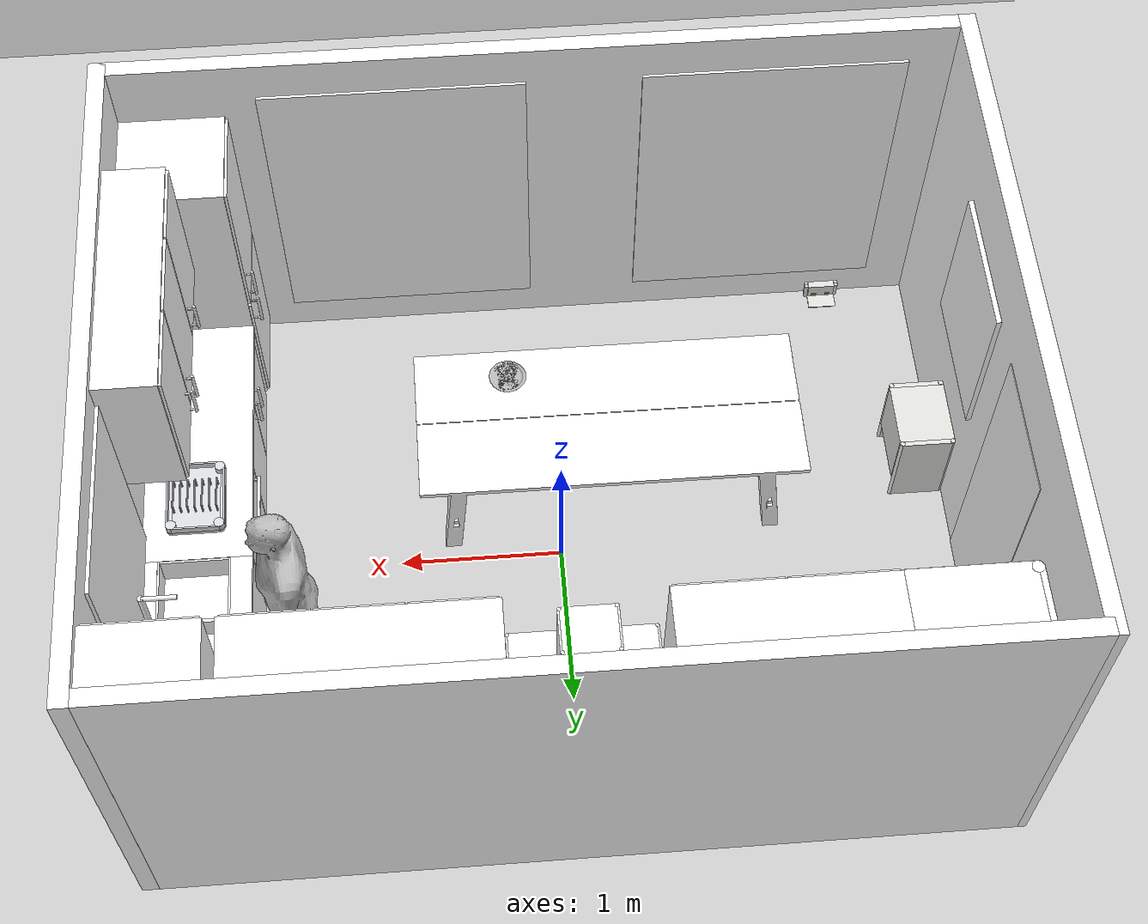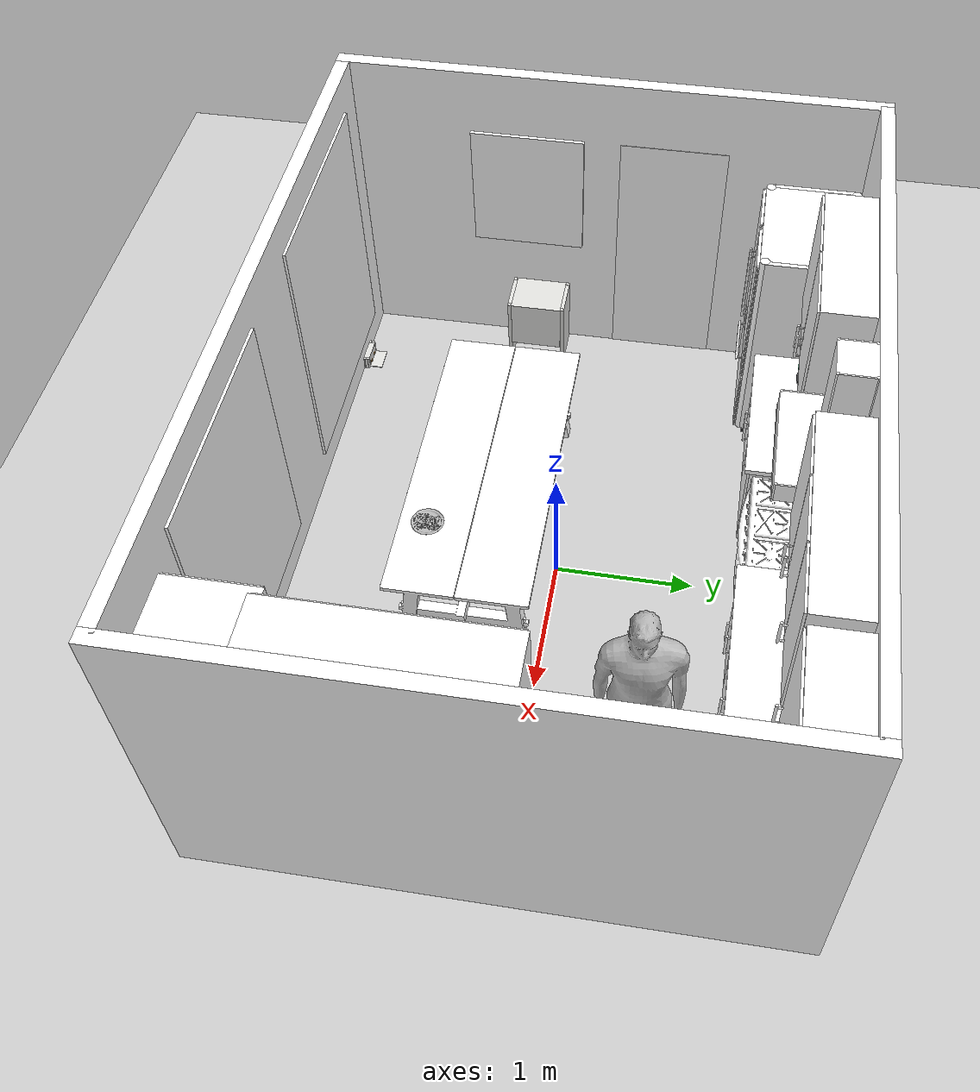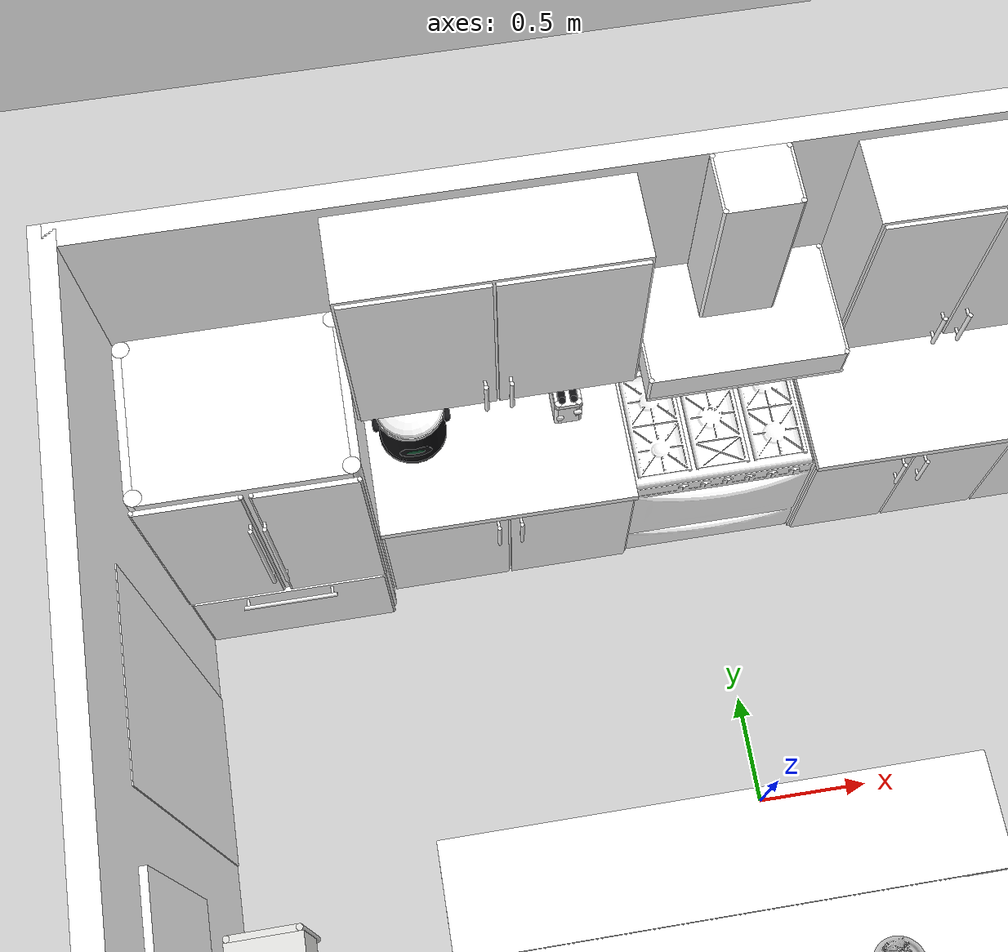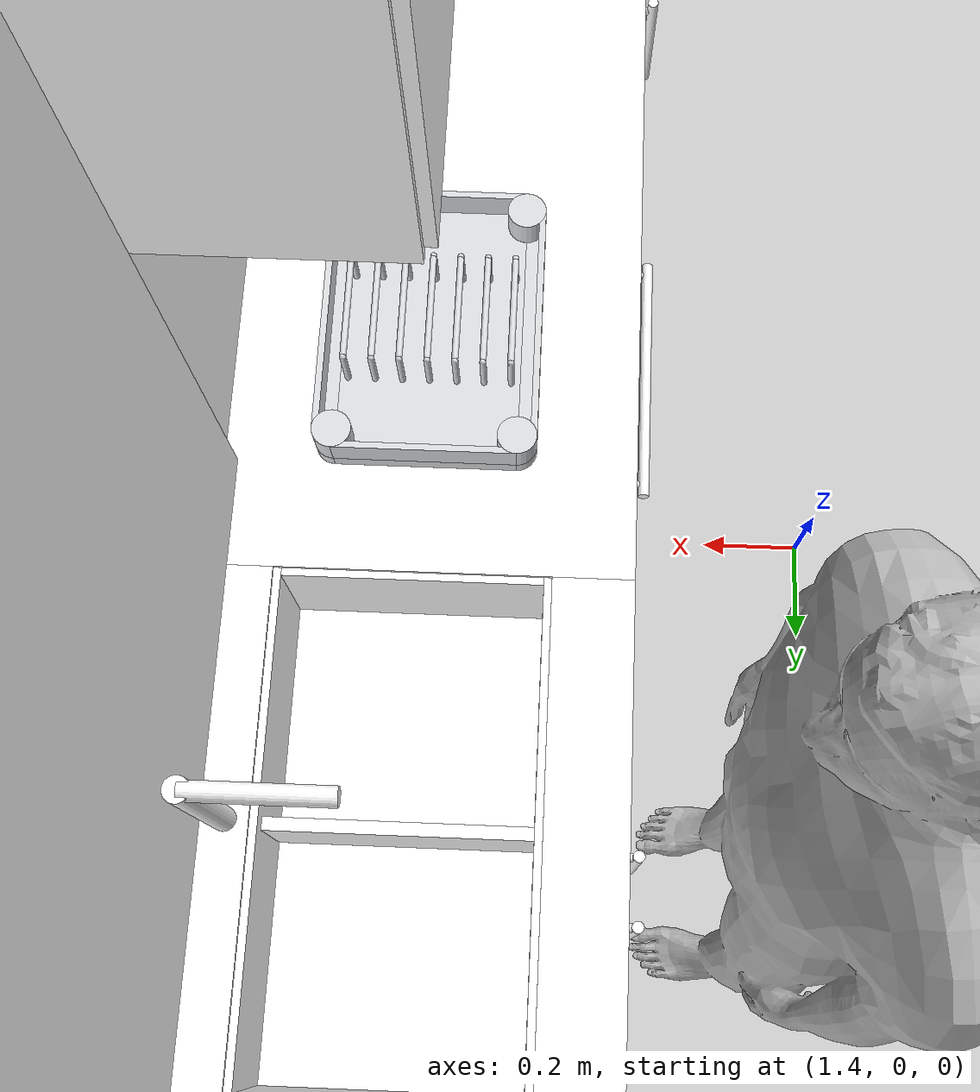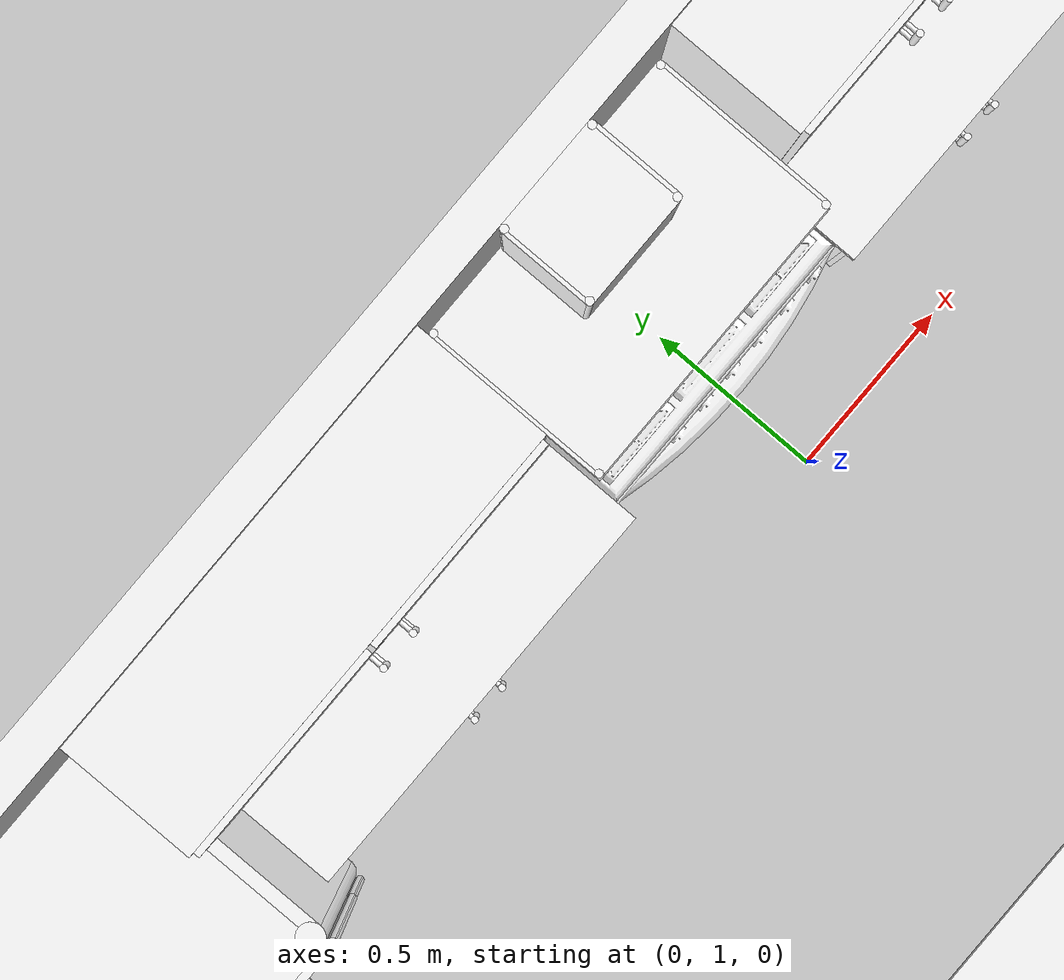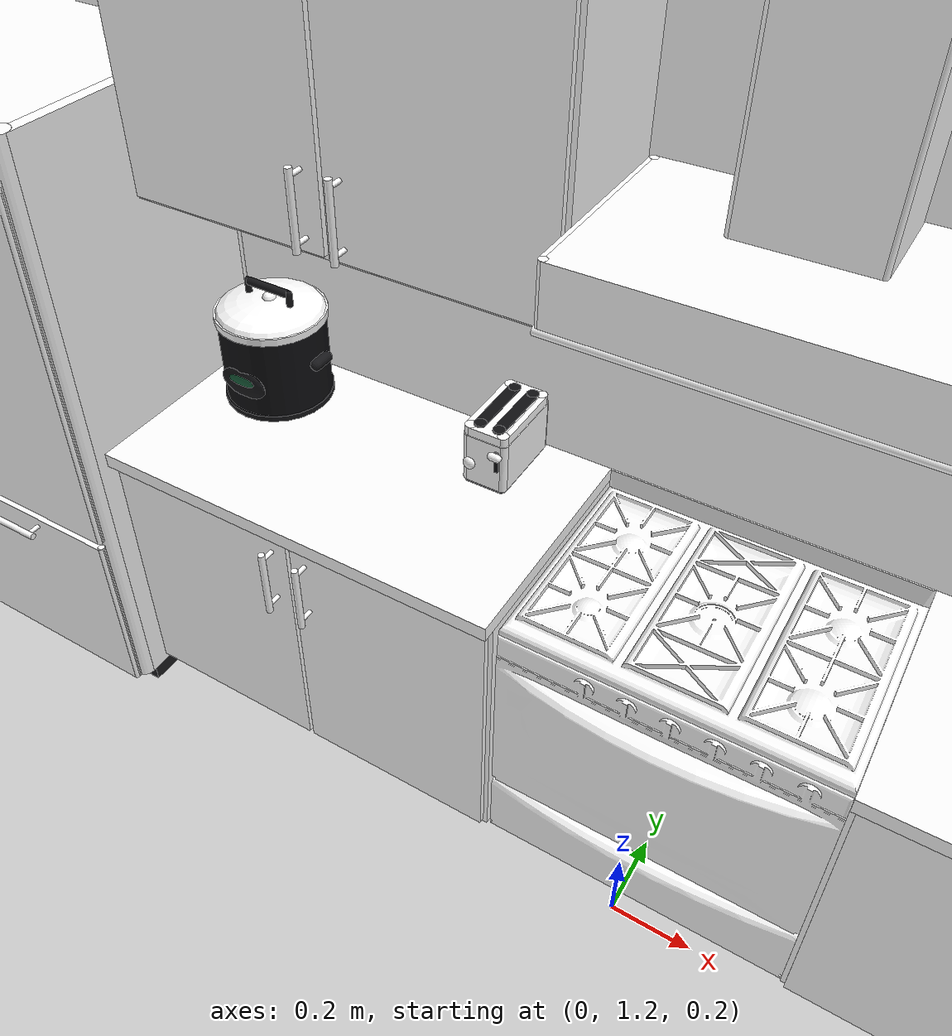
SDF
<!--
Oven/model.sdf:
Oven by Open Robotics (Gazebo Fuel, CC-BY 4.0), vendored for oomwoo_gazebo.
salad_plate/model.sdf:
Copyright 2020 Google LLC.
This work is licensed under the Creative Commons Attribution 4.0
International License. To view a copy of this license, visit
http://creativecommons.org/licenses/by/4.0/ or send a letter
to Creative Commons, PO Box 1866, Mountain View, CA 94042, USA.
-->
<sdf version="1.10">
 <world name="default">
  <scene>
   <shadows>false</shadows>
   <ambient>0.55 0.55 0.56 1</ambient>
   <background>0.699999988 0.699999988 0.699999988 1</background>
  </scene>
  <physics type="ode">
   <real_time_update_rate>1000</real_time_update_rate>
   <max_step_size>0.001</max_step_size>
   <real_time_factor>1</real_time_factor>
   <ode>
    <solver>
     <type>quick</type>
     <iters>150</iters>
     <precon_iters>0</precon_iters>
     <sor>1.3999999999999999</sor>
     <use_dynamic_moi_rescaling>true</use_dynamic_moi_rescaling>
    </solver>
    <constraints>
     <cfm>1.0000000000000001e-05</cfm>
     <erp>0.20000000000000001</erp>
     <contact_max_correcting_vel>2000</contact_max_correcting_vel>
     <contact_surface_layer>0.01</contact_surface_layer>
    </constraints>
   </ode>
  </physics>
  <plugin name="gz::sim::systems::Physics" filename="gz-sim-physics-system"/>
  <plugin name="gz::sim::systems::UserCommands" filename="gz-sim-user-commands-system"/>
  <plugin name="gz::sim::systems::SceneBroadcaster" filename="gz-sim-scene-broadcaster-system"/>
  <plugin name="gz::sim::systems::Sensors" filename="gz-sim-sensors-system">
   <render_engine>ogre2</render_engine>
  </plugin>
  <plugin name="gz::sim::systems::Imu" filename="gz-sim-imu-system"/>
  <plugin name="gz::sim::systems::Contact" filename="gz-sim-contact-system"/>
  <gravity>0 0 -9.8000000000000007</gravity>
  <magnetic_field>5.5644999999999998e-06 2.2875799999999999e-05 -4.2388400000000002e-05</magnetic_field>
  <atmosphere type="adiabatic"/>
  <include><uri>model://ground plane</uri><name>ground_plane</name></include>
  <light name="sun" type="directional">
   <cast_shadows>false</cast_shadows>
   <pose>0 0 10 0 -0 0</pose>
   <diffuse>0.8 0.8 0.8 1</diffuse>
   <specular>0.2 0.2 0.2 1</specular>
   <intensity>4</intensity>
   <attenuation>
    <range>1000</range>
    <constant>0.9</constant>
    <linear>0.01</linear>
    <quadratic>0.001</quadratic>
   </attenuation>
   <direction>-0.1 0.1 -0.9</direction>
   <spot><inner_angle>0</inner_angle><outer_angle>0</outer_angle><falloff>0</falloff></spot>
  </light>
  <light name="ceiling_light" type="point">
   <cast_shadows>false</cast_shadows>
   <pose>-0.2 0.1 2.4 0 -0 0</pose>
   <diffuse>1 0.97 0.92 1</diffuse>
   <specular>0.3 0.3 0.3 1</specular>
   <intensity>0.6</intensity>
   <attenuation>
    <range>8</range>
    <constant>0.35</constant>
    <linear>0.12</linear>
    <quadratic>0.03</quadratic>
   </attenuation>
  </light>
  <model name="wall_west">
   <static>true</static>
   <include><uri>model://room_wall_25x4m</uri></include>
   <pose>-2.5 0 1.25 0 -0 0</pose>
  </model>
  <model name="wall_east">
   <static>true</static>
   <include><uri>model://room_wall_25x4m</uri></include>
   <pose>2.5 0 1.25 0 -0 0</pose>
  </model>
  <model name="wall_south">
   <static>true</static>
   <include><uri>model://room_wall_25x5m</uri></include>
   <pose>0 -1.95 1.25 0 -0 1.5707</pose>
  </model>
  <model name="wall_north">
   <static>true</static>
   <include><uri>model://room_wall_25x5m</uri></include>
   <pose>0 1.95 1.25 0 -0 1.5707</pose>
  </model>
  <model name="door_08x2m">
   <static>true</static>
   <include><uri>model://door_08x2m</uri></include>
   <pose>-2.495 0.5 1 0 -0 0</pose>
  </model>
  <model name="vacuum_dock">
   <static>true</static>
   <include><uri>model://vacuum_dock</uri></include>
   <pose>-2.45 -0.5 0 0 -0 1.5708</pose>
  </model>
  <model name="charging_dock_basic">
   <static>true</static>
   <include><uri>model://charging_dock_basic</uri></include>
   <pose>-1.9 -1.9 0 0 -0 3.1416</pose>
  </model>
  <model name="makerspet_poster">
   <static>true</static>
   <include><uri>model://makerspet_poster</uri></include>
   <pose>-2.435 -0.6 1.5 0 -0 0</pose>
  </model>
  <model name="window_curtains_south_west">
   <static>true</static>
   <include><uri>model://window_curtains</uri></include>
   <pose>-1.4 -1.89 1.25 0 -0 1.5707</pose>
  </model>
  <model name="window_curtains_south_east">
   <static>true</static>
   <include><uri>model://window_curtains</uri></include>
   <pose>0.85 -1.89 1.25 0 -0 1.5707</pose>
  </model>
  <model name="window_curtains_east">
   <static>true</static>
   <include><uri>model://window_curtains_small</uri></include>
   <pose>2.44 0.75 1.6 0 -0 0</pose>
  </model>
  <model name="fridge_double_door">
   <static>true</static>
   <include><uri>model://fridge_double_door</uri></include>
   <pose>-2 1.9 0 0 -0 0</pose>
  </model>
  <model name="kitchen_base_run_w">
   <static>true</static>
   <include><uri>model://kitchen_base_run_w</uri></include>
   <pose>-0.978 1.9 0 0 -0 0</pose>
  </model>
  <model name="Oven">
   <static>true</static>
   <include><uri>model://Oven</uri></include>
   <pose>0 1.5811 0 0 -0 -1.5707</pose>
  </model>
  <model name="kitchen_base_run_e">
   <static>true</static>
   <include><uri>model://kitchen_base_run_e</uri></include>
   <pose>1.0965 1.9 0 0 -0 0</pose>
  </model>
  <model name="range_hood">
   <static>true</static>
   <include><uri>model://range_hood</uri></include>
   <pose>0 1.9 0 0 -0 0</pose>
  </model>
  <model name="kitchen_wall_cab_w">
   <static>true</static>
   <include><uri>model://kitchen_wall_cab_w</uri></include>
   <pose>-0.978 1.9 0 0 -0 0</pose>
  </model>
  <model name="kitchen_wall_cab_e">
   <static>true</static>
   <include><uri>model://kitchen_wall_cab_e</uri></include>
   <pose>1.0965 1.9 0 0 -0 0</pose>
  </model>
  <model name="kitchen_base_run_east">
   <static>true</static>
   <include><uri>model://kitchen_base_run_east</uri></include>
   <pose>2.45 0.325 0 0 -0 -1.5707</pose>
  </model>
  <model name="dishwasher">
   <static>true</static>
   <include><uri>model://dishwasher</uri></include>
   <pose>2.45 -0.02 0 0 -0 -1.5707</pose>
  </model>
  <model name="kitchen_wall_cab_ec">
   <static>true</static>
   <include><uri>model://kitchen_wall_cab_ec</uri></include>
   <pose>2.15 1.9 0 0 -0 0</pose>
  </model>
  <model name="kitchen_wall_cab_es">
   <static>true</static>
   <include><uri>model://kitchen_wall_cab_es</uri></include>
   <pose>2.45 -0.525 0 0 -0 -1.5707</pose>
  </model>
  <model name="kitchen_pantry">
   <static>true</static>
   <include><uri>model://kitchen_pantry</uri></include>
   <pose>2.45 -1.6 0 0 -0 -1.5707</pose>
  </model>
  <model name="DiningTable">
   <static>true</static>
   <include><uri>model://DiningTable</uri></include>
   <pose>-0.33 -0.55 0 0 -0 1.5707</pose>
  </model>
  <model name="person_standing">
   <static>true</static>
   <include><uri>model://person_standing</uri></include>
   <pose>1.5 0.75 0 0 -0 1.5708</pose>
  </model>
  <model name="salad_plate">
   <static>true</static>
   <include><uri>model://salad_plate</uri></include>
   <pose>0.27 -0.85 0.74 0 -0 0</pose>
  </model>
  <model name="pressure_cooker">
   <static>true</static>
   <include><uri>model://pressure_cooker</uri></include>
   <pose>-1.34 1.73 0.9 0 -0 0</pose>
  </model>
  <model name="toaster_4_slice">
   <static>true</static>
   <include><uri>model://toaster_4_slice</uri></include>
   <pose>-0.65 1.78 0.9 0 -0 0</pose>
  </model>
  <model name="dish_drainer">
   <static>true</static>
   <include><uri>model://dish_drainer</uri></include>
   <pose>2.14 -0.02 0.9 0 -0 0</pose>
  </model>
 </world>
</sdf>

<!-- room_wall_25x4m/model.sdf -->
<sdf version='1.4'>
  <model name='room_wall_25x4m'>
    <link name="link">
      <visual name="visual">
        <geometry>
          <box>
            <size>0.1 4.0 2.5</size>
          </box>
        </geometry>
        <material>
          <pbr>
            <metal>
              <albedo_map>textures/wall_texture_25x4m.jpg</albedo_map>
            <metalness>0.0</metalness><roughness>0.90</roughness>
            </metal>
          </pbr>
          <ambient>1 1 1 1</ambient>
          <diffuse>1 1 1 1</diffuse>
          <specular>1 1 1 1</specular>
          <emissive>0 0 0 1</emissive>
        </material>
        <cast_shadows>1</cast_shadows>
        <transparency>0</transparency>
      </visual>
      <collision name ="collision">
        <geometry>
           <box>
            <size>0.1 4.0 2.5</size>
          </box>
        </geometry>
      </collision>
    </link>
    <static>1</static>
    <allow_auto_disable>1</allow_auto_disable>
  </model>
</sdf>

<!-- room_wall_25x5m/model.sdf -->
<sdf version='1.4'>
  <model name='room_wall_25x5m'>
    <link name="link">
      <visual name="visual">
        <geometry>
          <box>
            <size>0.1 5.0 2.5</size>
          </box>
        </geometry>
        <material>
          <pbr>
            <metal>
              <albedo_map>textures/wall_texture_25x5m.jpg</albedo_map>
            <metalness>0.0</metalness><roughness>0.90</roughness>
            </metal>
          </pbr>
          <ambient>1 1 1 1</ambient>
          <diffuse>1 1 1 1</diffuse>
          <specular>1 1 1 1</specular>
          <emissive>0 0 0 1</emissive>
        </material>
        <cast_shadows>1</cast_shadows>
        <transparency>0</transparency>
      </visual>
      <collision name ="collision">
        <geometry>
           <box>
            <size>0.1 5.0 2.5</size>
          </box>
        </geometry>
      </collision>
    </link>
    <static>1</static>
    <allow_auto_disable>1</allow_auto_disable>
  </model>
</sdf>

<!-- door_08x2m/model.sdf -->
<sdf version='1.4'>
  <model name='door_08x2m'>
    <link name="link">
      <visual name="visual">
        <geometry>
          <box>
            <size>0.1 0.8 2</size>
          </box>
        </geometry>
        <material>
          <pbr>
            <metal>
              <albedo_map>textures/door_08x2m.png</albedo_map>
            <metalness>0.0</metalness><roughness>0.70</roughness>
            </metal>
          </pbr>
          <ambient>1 1 1 1</ambient>
          <diffuse>1 1 1 1</diffuse>
          <specular>1 1 1 1</specular>
          <emissive>0 0 0 1</emissive>
        </material>
        <cast_shadows>1</cast_shadows>
        <transparency>0</transparency>
      </visual>
    </link>
    <static>1</static>
    <allow_auto_disable>1</allow_auto_disable>
  </model>
</sdf>

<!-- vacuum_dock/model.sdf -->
<sdf version="1.6">
  <model name="vacuum_dock">
    <static>true</static>
    <link name="link">
      <visual name="core">
        <pose>0 -0.17 0.375 0 0 0</pose>
        <geometry><box><size>0.4 0.34 0.41</size></box></geometry>
        <material><pbr><metal><metalness>0.00</metalness><roughness>0.35</roughness></metal></pbr><ambient>0.880 0.880 0.870 1</ambient><diffuse>0.880 0.880 0.870 1</diffuse><specular>0.35 0.35 0.35 1</specular><emissive>0 0 0 1</emissive></material>
      </visual>
      <visual name="side0">
        <pose>-0.215 -0.17 0.29 0 0 0</pose>
        <geometry><box><size>0.03 0.31 0.58</size></box></geometry>
        <material><pbr><metal><metalness>0.00</metalness><roughness>0.35</roughness></metal></pbr><ambient>0.880 0.880 0.870 1</ambient><diffuse>0.880 0.880 0.870 1</diffuse><specular>0.35 0.35 0.35 1</specular><emissive>0 0 0 1</emissive></material>
      </visual>
      <visual name="side1">
        <pose>0.215 -0.17 0.29 0 0 0</pose>
        <geometry><box><size>0.03 0.31 0.58</size></box></geometry>
        <material><pbr><metal><metalness>0.00</metalness><roughness>0.35</roughness></metal></pbr><ambient>0.880 0.880 0.870 1</ambient><diffuse>0.880 0.880 0.870 1</diffuse><specular>0.35 0.35 0.35 1</specular><emissive>0 0 0 1</emissive></material>
      </visual>
      <visual name="tube0">
        <pose>-0.215 -0.015 0.29 0 0 0</pose>
        <geometry><cylinder><radius>0.015</radius><length>0.584</length></cylinder></geometry>
        <material><pbr><metal><metalness>0.00</metalness><roughness>0.35</roughness></metal></pbr><ambient>0.880 0.880 0.870 1</ambient><diffuse>0.880 0.880 0.870 1</diffuse><specular>0.35 0.35 0.35 1</specular><emissive>0 0 0 1</emissive></material>
      </visual>
      <visual name="tube1">
        <pose>-0.215 -0.325 0.29 0 0 0</pose>
        <geometry><cylinder><radius>0.015</radius><length>0.584</length></cylinder></geometry>
        <material><pbr><metal><metalness>0.00</metalness><roughness>0.35</roughness></metal></pbr><ambient>0.880 0.880 0.870 1</ambient><diffuse>0.880 0.880 0.870 1</diffuse><specular>0.35 0.35 0.35 1</specular><emissive>0 0 0 1</emissive></material>
      </visual>
      <visual name="tube2">
        <pose>0.215 -0.015 0.29 0 0 0</pose>
        <geometry><cylinder><radius>0.015</radius><length>0.584</length></cylinder></geometry>
        <material><pbr><metal><metalness>0.00</metalness><roughness>0.35</roughness></metal></pbr><ambient>0.880 0.880 0.870 1</ambient><diffuse>0.880 0.880 0.870 1</diffuse><specular>0.35 0.35 0.35 1</specular><emissive>0 0 0 1</emissive></material>
      </visual>
      <visual name="tube3">
        <pose>0.215 -0.325 0.29 0 0 0</pose>
        <geometry><cylinder><radius>0.015</radius><length>0.584</length></cylinder></geometry>
        <material><pbr><metal><metalness>0.00</metalness><roughness>0.35</roughness></metal></pbr><ambient>0.880 0.880 0.870 1</ambient><diffuse>0.880 0.880 0.870 1</diffuse><specular>0.35 0.35 0.35 1</specular><emissive>0 0 0 1</emissive></material>
      </visual>
      <visual name="back_spacer">
        <pose>0 -0.05 0.085 0 0 0</pose>
        <geometry><box><size>0.4 0.1 0.17</size></box></geometry>
        <material><pbr><metal><metalness>0.00</metalness><roughness>0.55</roughness></metal></pbr><ambient>0.130 0.130 0.140 1</ambient><diffuse>0.130 0.130 0.140 1</diffuse><specular>0.35 0.35 0.35 1</specular><emissive>0 0 0 1</emissive></material>
      </visual>
      <collision name="core">
        <pose>0 -0.17 0.375 0 0 0</pose>
        <geometry><box><size>0.4 0.34 0.41</size></box></geometry>
      </collision>
      <collision name="side0">
        <pose>-0.215 -0.17 0.29 0 0 0</pose>
        <geometry><box><size>0.03 0.34 0.58</size></box></geometry>
      </collision>
      <collision name="side1">
        <pose>0.215 -0.17 0.29 0 0 0</pose>
        <geometry><box><size>0.03 0.34 0.58</size></box></geometry>
      </collision>
      <collision name="back_spacer">
        <pose>0 -0.05 0.085 0 0 0</pose>
        <geometry><box><size>0.4 0.1 0.17</size></box></geometry>
      </collision>
    </link>
    <allow_auto_disable>1</allow_auto_disable>
  </model>
</sdf>

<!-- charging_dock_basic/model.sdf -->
<sdf version="1.6">
  <model name="charging_dock_basic">
    <static>true</static>
    <link name="link">
      <visual name="core">
        <pose>0 -0.024 0.049 0 0 0</pose>
        <geometry><box><size>0.172 0.048 0.098</size></box></geometry>
        <material><pbr><metal><metalness>0.00</metalness><roughness>0.35</roughness></metal></pbr><ambient>0.880 0.880 0.870 1</ambient><diffuse>0.880 0.880 0.870 1</diffuse><specular>0.35 0.35 0.35 1</specular><emissive>0 0 0 1</emissive></material>
      </visual>
      <visual name="side0">
        <pose>-0.098 -0.024 0.049 0 0 0</pose>
        <geometry><box><size>0.024 0.024 0.098</size></box></geometry>
        <material><pbr><metal><metalness>0.00</metalness><roughness>0.35</roughness></metal></pbr><ambient>0.880 0.880 0.870 1</ambient><diffuse>0.880 0.880 0.870 1</diffuse><specular>0.35 0.35 0.35 1</specular><emissive>0 0 0 1</emissive></material>
      </visual>
      <visual name="side1">
        <pose>0.098 -0.024 0.049 0 0 0</pose>
        <geometry><box><size>0.024 0.024 0.098</size></box></geometry>
        <material><pbr><metal><metalness>0.00</metalness><roughness>0.35</roughness></metal></pbr><ambient>0.880 0.880 0.870 1</ambient><diffuse>0.880 0.880 0.870 1</diffuse><specular>0.35 0.35 0.35 1</specular><emissive>0 0 0 1</emissive></material>
      </visual>
      <visual name="tube0">
        <pose>-0.098 -0.012 0.049 0 0 0</pose>
        <geometry><cylinder><radius>0.012</radius><length>0.102</length></cylinder></geometry>
        <material><pbr><metal><metalness>0.00</metalness><roughness>0.35</roughness></metal></pbr><ambient>0.880 0.880 0.870 1</ambient><diffuse>0.880 0.880 0.870 1</diffuse><specular>0.35 0.35 0.35 1</specular><emissive>0 0 0 1</emissive></material>
      </visual>
      <visual name="tube1">
        <pose>-0.098 -0.036 0.049 0 0 0</pose>
        <geometry><cylinder><radius>0.012</radius><length>0.102</length></cylinder></geometry>
        <material><pbr><metal><metalness>0.00</metalness><roughness>0.35</roughness></metal></pbr><ambient>0.880 0.880 0.870 1</ambient><diffuse>0.880 0.880 0.870 1</diffuse><specular>0.35 0.35 0.35 1</specular><emissive>0 0 0 1</emissive></material>
      </visual>
      <visual name="tube2">
        <pose>0.098 -0.012 0.049 0 0 0</pose>
        <geometry><cylinder><radius>0.012</radius><length>0.102</length></cylinder></geometry>
        <material><pbr><metal><metalness>0.00</metalness><roughness>0.35</roughness></metal></pbr><ambient>0.880 0.880 0.870 1</ambient><diffuse>0.880 0.880 0.870 1</diffuse><specular>0.35 0.35 0.35 1</specular><emissive>0 0 0 1</emissive></material>
      </visual>
      <visual name="tube3">
        <pose>0.098 -0.036 0.049 0 0 0</pose>
        <geometry><cylinder><radius>0.012</radius><length>0.102</length></cylinder></geometry>
        <material><pbr><metal><metalness>0.00</metalness><roughness>0.35</roughness></metal></pbr><ambient>0.880 0.880 0.870 1</ambient><diffuse>0.880 0.880 0.870 1</diffuse><specular>0.35 0.35 0.35 1</specular><emissive>0 0 0 1</emissive></material>
      </visual>
      <visual name="plate">
        <pose>0 -0.0965 0.003 0 0 0</pose>
        <geometry><box><size>0.18 0.097 0.006</size></box></geometry>
        <material><pbr><metal><metalness>0.00</metalness><roughness>0.35</roughness></metal></pbr><ambient>0.880 0.880 0.870 1</ambient><diffuse>0.880 0.880 0.870 1</diffuse><specular>0.35 0.35 0.35 1</specular><emissive>0 0 0 1</emissive></material>
      </visual>
      <visual name="contact0">
        <pose>-0.045 -0.051 0.022 0 0 0</pose>
        <geometry><box><size>0.032 0.006 0.018</size></box></geometry>
        <material><pbr><metal><metalness>0.70</metalness><roughness>0.20</roughness></metal></pbr><ambient>0.720 0.550 0.300 1</ambient><diffuse>0.720 0.550 0.300 1</diffuse><specular>0.35 0.35 0.35 1</specular><emissive>0 0 0 1</emissive></material>
      </visual>
      <visual name="contact1">
        <pose>0.045 -0.051 0.022 0 0 0</pose>
        <geometry><box><size>0.032 0.006 0.018</size></box></geometry>
        <material><pbr><metal><metalness>0.70</metalness><roughness>0.20</roughness></metal></pbr><ambient>0.720 0.550 0.300 1</ambient><diffuse>0.720 0.550 0.300 1</diffuse><specular>0.35 0.35 0.35 1</specular><emissive>0 0 0 1</emissive></material>
      </visual>
      <collision name="panel">
        <pose>0 -0.024 0.049 0 0 0</pose>
        <geometry><box><size>0.22 0.048 0.098</size></box></geometry>
      </collision>
    </link>
    <allow_auto_disable>1</allow_auto_disable>
  </model>
</sdf>

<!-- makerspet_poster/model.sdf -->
<sdf version='1.4'>
  <model name='makerspet_poster'>
    <link name="link">
      <visual name="visual">
        <geometry>
          <box>
            <size>0.03 0.85714 1</size>
          </box>
        </geometry>
        <material>
          <pbr>
            <metal>
              <albedo_map>textures/makerspet_logo_600x700.png</albedo_map>
            <metalness>0.0</metalness><roughness>0.80</roughness>
            </metal>
          </pbr>
          <ambient>1 1 1 1</ambient>
          <diffuse>1 1 1 1</diffuse>
          <specular>1 1 1 1</specular>
          <emissive>0 0 0 1</emissive>
        </material>
      </visual>
    </link>
    <static>1</static>
    <allow_auto_disable>1</allow_auto_disable>
  </model>
</sdf>

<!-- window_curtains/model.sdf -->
<sdf version='1.4'>
  <model name='window_curtains'>
    <link name="link">
      <visual name="visual">
        <geometry>
          <box>
            <size>0.02 1.5676 2</size>
          </box>
        </geometry>
        <material>
          <pbr>
            <metal>
              <emissive_map>textures/window_curtains.png</emissive_map>
            <metalness>0.0</metalness><roughness>0.95</roughness>
            </metal>
          </pbr>
          <ambient>1 1 1 1</ambient>
          <diffuse>1 1 1 1</diffuse>
          <specular>1 1 1 1</specular>
          <emissive>0.4 0.4 0.4 1</emissive>
        </material>
      </visual>
    </link>
    <static>1</static>
    <allow_auto_disable>1</allow_auto_disable>
  </model>
</sdf>

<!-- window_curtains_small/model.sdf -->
<sdf version="1.4">
  <model name="window_curtains_small">
    <static>true</static>
    <link name="link">
      <visual name="visual">
        <pose>0 0 0 0 0 0</pose>
        <geometry><box><size>0.02 1.10 1.40</size></box></geometry>
        <material><pbr><metal><emissive_map>textures/window_curtains.png</emissive_map></metal></pbr><ambient>1 1 1 1</ambient><diffuse>1 1 1 1</diffuse><specular>1 1 1 1</specular><emissive>0.4 0.4 0.4 1</emissive></material>
      </visual>
    </link>
    <allow_auto_disable>1</allow_auto_disable>
  </model>
</sdf>

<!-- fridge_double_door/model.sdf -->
<sdf version="1.6">
  <model name="fridge_double_door">
    <static>true</static>
    <link name="link">
      <visual name="plinth">
        <pose>0 -0.325 0.03 0 0 0</pose>
        <geometry><box><size>0.88 0.65 0.06</size></box></geometry>
        <material><ambient>0.11 0.11 0.12 1</ambient><diffuse>0.11 0.11 0.12 1</diffuse><specular>0.05 0.05 0.05 1</specular><emissive>0 0 0 1</emissive></material>
      </visual>
      <visual name="body_a">
        <pose>0 -0.35 0.92 0 0 0</pose>
        <geometry><box><size>0.83 0.7 1.72</size></box></geometry>
        <material><pbr><metal><albedo_map>textures/stainless.png</albedo_map><metalness>0.15</metalness><roughness>0.25</roughness></metal></pbr><ambient>1 1 1 1</ambient><diffuse>1 1 1 1</diffuse><specular>1 1 1 1</specular><emissive>0 0 0 1</emissive></material>
      </visual>
      <visual name="body_b0">
        <pose>-0.4325 -0.35 0.92 0 0 0</pose>
        <geometry><box><size>0.035 0.63 1.72</size></box></geometry>
        <material><pbr><metal><albedo_map>textures/stainless.png</albedo_map><metalness>0.15</metalness><roughness>0.25</roughness></metal></pbr><ambient>1 1 1 1</ambient><diffuse>1 1 1 1</diffuse><specular>1 1 1 1</specular><emissive>0 0 0 1</emissive></material>
      </visual>
      <visual name="body_b1">
        <pose>0.4325 -0.35 0.92 0 0 0</pose>
        <geometry><box><size>0.035 0.63 1.72</size></box></geometry>
        <material><pbr><metal><albedo_map>textures/stainless.png</albedo_map><metalness>0.15</metalness><roughness>0.25</roughness></metal></pbr><ambient>1 1 1 1</ambient><diffuse>1 1 1 1</diffuse><specular>1 1 1 1</specular><emissive>0 0 0 1</emissive></material>
      </visual>
      <visual name="body_c0">
        <pose>-0.415 -0.665 0.92 0 0 0</pose>
        <geometry><cylinder><radius>0.035</radius><length>1.7206</length></cylinder></geometry>
        <material><pbr><metal><albedo_map>textures/stainless.png</albedo_map><metalness>0.15</metalness><roughness>0.25</roughness></metal></pbr><ambient>1 1 1 1</ambient><diffuse>1 1 1 1</diffuse><specular>1 1 1 1</specular><emissive>0 0 0 1</emissive></material>
      </visual>
      <visual name="body_c1">
        <pose>-0.415 -0.035 0.92 0 0 0</pose>
        <geometry><cylinder><radius>0.035</radius><length>1.7208</length></cylinder></geometry>
        <material><pbr><metal><albedo_map>textures/stainless.png</albedo_map><metalness>0.15</metalness><roughness>0.25</roughness></metal></pbr><ambient>1 1 1 1</ambient><diffuse>1 1 1 1</diffuse><specular>1 1 1 1</specular><emissive>0 0 0 1</emissive></material>
      </visual>
      <visual name="body_c2">
        <pose>0.415 -0.665 0.92 0 0 0</pose>
        <geometry><cylinder><radius>0.035</radius><length>1.721</length></cylinder></geometry>
        <material><pbr><metal><albedo_map>textures/stainless.png</albedo_map><metalness>0.15</metalness><roughness>0.25</roughness></metal></pbr><ambient>1 1 1 1</ambient><diffuse>1 1 1 1</diffuse><specular>1 1 1 1</specular><emissive>0 0 0 1</emissive></material>
      </visual>
      <visual name="body_c3">
        <pose>0.415 -0.035 0.92 0 0 0</pose>
        <geometry><cylinder><radius>0.035</radius><length>1.7211</length></cylinder></geometry>
        <material><pbr><metal><albedo_map>textures/stainless.png</albedo_map><metalness>0.15</metalness><roughness>0.25</roughness></metal></pbr><ambient>1 1 1 1</ambient><diffuse>1 1 1 1</diffuse><specular>1 1 1 1</specular><emissive>0 0 0 1</emissive></material>
      </visual>
      <visual name="freezer_front_a">
        <pose>0 -0.711 0.345 0 0 0</pose>
        <geometry><box><size>0.862 0.022 0.54</size></box></geometry>
        <material><pbr><metal><albedo_map>textures/stainless.png</albedo_map><metalness>0.15</metalness><roughness>0.25</roughness></metal></pbr><ambient>1 1 1 1</ambient><diffuse>1 1 1 1</diffuse><specular>1 1 1 1</specular><emissive>0 0 0 1</emissive></material>
      </visual>
      <visual name="freezer_front_b0">
        <pose>-0.4355 -0.711 0.345 0 0 0</pose>
        <geometry><box><size>0.009 0.004 0.54</size></box></geometry>
        <material><pbr><metal><albedo_map>textures/stainless.png</albedo_map><metalness>0.15</metalness><roughness>0.25</roughness></metal></pbr><ambient>1 1 1 1</ambient><diffuse>1 1 1 1</diffuse><specular>1 1 1 1</specular><emissive>0 0 0 1</emissive></material>
      </visual>
      <visual name="freezer_front_b1">
        <pose>0.4355 -0.711 0.345 0 0 0</pose>
        <geometry><box><size>0.009 0.004 0.54</size></box></geometry>
        <material><pbr><metal><albedo_map>textures/stainless.png</albedo_map><metalness>0.15</metalness><roughness>0.25</roughness></metal></pbr><ambient>1 1 1 1</ambient><diffuse>1 1 1 1</diffuse><specular>1 1 1 1</specular><emissive>0 0 0 1</emissive></material>
      </visual>
      <visual name="freezer_front_c0">
        <pose>-0.431 -0.713 0.345 0 0 0</pose>
        <geometry><cylinder><radius>0.009</radius><length>0.5406</length></cylinder></geometry>
        <material><pbr><metal><albedo_map>textures/stainless.png</albedo_map><metalness>0.15</metalness><roughness>0.25</roughness></metal></pbr><ambient>1 1 1 1</ambient><diffuse>1 1 1 1</diffuse><specular>1 1 1 1</specular><emissive>0 0 0 1</emissive></material>
      </visual>
      <visual name="freezer_front_c1">
        <pose>-0.431 -0.709 0.345 0 0 0</pose>
        <geometry><cylinder><radius>0.009</radius><length>0.54078</length></cylinder></geometry>
        <material><pbr><metal><albedo_map>textures/stainless.png</albedo_map><metalness>0.15</metalness><roughness>0.25</roughness></metal></pbr><ambient>1 1 1 1</ambient><diffuse>1 1 1 1</diffuse><specular>1 1 1 1</specular><emissive>0 0 0 1</emissive></material>
      </visual>
      <visual name="freezer_front_c2">
        <pose>0.431 -0.713 0.345 0 0 0</pose>
        <geometry><cylinder><radius>0.009</radius><length>0.54096</length></cylinder></geometry>
        <material><pbr><metal><albedo_map>textures/stainless.png</albedo_map><metalness>0.15</metalness><roughness>0.25</roughness></metal></pbr><ambient>1 1 1 1</ambient><diffuse>1 1 1 1</diffuse><specular>1 1 1 1</specular><emissive>0 0 0 1</emissive></material>
      </visual>
      <visual name="freezer_front_c3">
        <pose>0.431 -0.709 0.345 0 0 0</pose>
        <geometry><cylinder><radius>0.009</radius><length>0.54114</length></cylinder></geometry>
        <material><pbr><metal><albedo_map>textures/stainless.png</albedo_map><metalness>0.15</metalness><roughness>0.25</roughness></metal></pbr><ambient>1 1 1 1</ambient><diffuse>1 1 1 1</diffuse><specular>1 1 1 1</specular><emissive>0 0 0 1</emissive></material>
      </visual>
      <visual name="freezer_handle_bar">
        <pose>0 -0.76 0.585 0 1.5708 0</pose>
        <geometry><cylinder><radius>0.009</radius><length>0.42</length></cylinder></geometry>
        <material><pbr><metal><albedo_map>textures/stainless.png</albedo_map><metalness>0.25</metalness><roughness>0.15</roughness></metal></pbr><ambient>1 1 1 1</ambient><diffuse>1 1 1 1</diffuse><specular>1 1 1 1</specular><emissive>0 0 0 1</emissive></material>
      </visual>
      <visual name="freezer_handle_post0">
        <pose>-0.19 -0.741 0.585 1.5708 0 0</pose>
        <geometry><cylinder><radius>0.0063</radius><length>0.038</length></cylinder></geometry>
        <material><pbr><metal><albedo_map>textures/stainless.png</albedo_map><metalness>0.25</metalness><roughness>0.15</roughness></metal></pbr><ambient>1 1 1 1</ambient><diffuse>1 1 1 1</diffuse><specular>1 1 1 1</specular><emissive>0 0 0 1</emissive></material>
      </visual>
      <visual name="freezer_handle_post1">
        <pose>0.19 -0.741 0.585 1.5708 0 0</pose>
        <geometry><cylinder><radius>0.0063</radius><length>0.038</length></cylinder></geometry>
        <material><pbr><metal><albedo_map>textures/stainless.png</albedo_map><metalness>0.25</metalness><roughness>0.15</roughness></metal></pbr><ambient>1 1 1 1</ambient><diffuse>1 1 1 1</diffuse><specular>1 1 1 1</specular><emissive>0 0 0 1</emissive></material>
      </visual>
      <visual name="door0_a">
        <pose>-0.228 -0.711 1.19 0 0 0</pose>
        <geometry><box><size>0.416 0.022 1.1</size></box></geometry>
        <material><pbr><metal><albedo_map>textures/stainless.png</albedo_map><metalness>0.15</metalness><roughness>0.25</roughness></metal></pbr><ambient>1 1 1 1</ambient><diffuse>1 1 1 1</diffuse><specular>1 1 1 1</specular><emissive>0 0 0 1</emissive></material>
      </visual>
      <visual name="door0_b0">
        <pose>-0.4405 -0.711 1.19 0 0 0</pose>
        <geometry><box><size>0.009 0.004 1.1</size></box></geometry>
        <material><pbr><metal><albedo_map>textures/stainless.png</albedo_map><metalness>0.15</metalness><roughness>0.25</roughness></metal></pbr><ambient>1 1 1 1</ambient><diffuse>1 1 1 1</diffuse><specular>1 1 1 1</specular><emissive>0 0 0 1</emissive></material>
      </visual>
      <visual name="door0_b1">
        <pose>-0.0155 -0.711 1.19 0 0 0</pose>
        <geometry><box><size>0.009 0.004 1.1</size></box></geometry>
        <material><pbr><metal><albedo_map>textures/stainless.png</albedo_map><metalness>0.15</metalness><roughness>0.25</roughness></metal></pbr><ambient>1 1 1 1</ambient><diffuse>1 1 1 1</diffuse><specular>1 1 1 1</specular><emissive>0 0 0 1</emissive></material>
      </visual>
      <visual name="door0_c0">
        <pose>-0.436 -0.713 1.19 0 0 0</pose>
        <geometry><cylinder><radius>0.009</radius><length>1.1006</length></cylinder></geometry>
        <material><pbr><metal><albedo_map>textures/stainless.png</albedo_map><metalness>0.15</metalness><roughness>0.25</roughness></metal></pbr><ambient>1 1 1 1</ambient><diffuse>1 1 1 1</diffuse><specular>1 1 1 1</specular><emissive>0 0 0 1</emissive></material>
      </visual>
      <visual name="door0_c1">
        <pose>-0.436 -0.709 1.19 0 0 0</pose>
        <geometry><cylinder><radius>0.009</radius><length>1.1008</length></cylinder></geometry>
        <material><pbr><metal><albedo_map>textures/stainless.png</albedo_map><metalness>0.15</metalness><roughness>0.25</roughness></metal></pbr><ambient>1 1 1 1</ambient><diffuse>1 1 1 1</diffuse><specular>1 1 1 1</specular><emissive>0 0 0 1</emissive></material>
      </visual>
      <visual name="door0_c2">
        <pose>-0.02 -0.713 1.19 0 0 0</pose>
        <geometry><cylinder><radius>0.009</radius><length>1.101</length></cylinder></geometry>
        <material><pbr><metal><albedo_map>textures/stainless.png</albedo_map><metalness>0.15</metalness><roughness>0.25</roughness></metal></pbr><ambient>1 1 1 1</ambient><diffuse>1 1 1 1</diffuse><specular>1 1 1 1</specular><emissive>0 0 0 1</emissive></material>
      </visual>
      <visual name="door0_c3">
        <pose>-0.02 -0.709 1.19 0 0 0</pose>
        <geometry><cylinder><radius>0.009</radius><length>1.1011</length></cylinder></geometry>
        <material><pbr><metal><albedo_map>textures/stainless.png</albedo_map><metalness>0.15</metalness><roughness>0.25</roughness></metal></pbr><ambient>1 1 1 1</ambient><diffuse>1 1 1 1</diffuse><specular>1 1 1 1</specular><emissive>0 0 0 1</emissive></material>
      </visual>
      <visual name="door0_handle_bar">
        <pose>-0.028 -0.76 1.19 0 0 0</pose>
        <geometry><cylinder><radius>0.009</radius><length>0.62</length></cylinder></geometry>
        <material><pbr><metal><albedo_map>textures/stainless.png</albedo_map><metalness>0.25</metalness><roughness>0.15</roughness></metal></pbr><ambient>1 1 1 1</ambient><diffuse>1 1 1 1</diffuse><specular>1 1 1 1</specular><emissive>0 0 0 1</emissive></material>
      </visual>
      <visual name="door0_handle_post0">
        <pose>-0.028 -0.741 0.9 1.5708 0 0</pose>
        <geometry><cylinder><radius>0.0063</radius><length>0.038</length></cylinder></geometry>
        <material><pbr><metal><albedo_map>textures/stainless.png</albedo_map><metalness>0.25</metalness><roughness>0.15</roughness></metal></pbr><ambient>1 1 1 1</ambient><diffuse>1 1 1 1</diffuse><specular>1 1 1 1</specular><emissive>0 0 0 1</emissive></material>
      </visual>
      <visual name="door0_handle_post1">
        <pose>-0.028 -0.741 1.48 1.5708 0 0</pose>
        <geometry><cylinder><radius>0.0063</radius><length>0.038</length></cylinder></geometry>
        <material><pbr><metal><albedo_map>textures/stainless.png</albedo_map><metalness>0.25</metalness><roughness>0.15</roughness></metal></pbr><ambient>1 1 1 1</ambient><diffuse>1 1 1 1</diffuse><specular>1 1 1 1</specular><emissive>0 0 0 1</emissive></material>
      </visual>
      <visual name="door1_a">
        <pose>0.228 -0.711 1.19 0 0 0</pose>
        <geometry><box><size>0.416 0.022 1.1</size></box></geometry>
        <material><pbr><metal><albedo_map>textures/stainless.png</albedo_map><metalness>0.15</metalness><roughness>0.25</roughness></metal></pbr><ambient>1 1 1 1</ambient><diffuse>1 1 1 1</diffuse><specular>1 1 1 1</specular><emissive>0 0 0 1</emissive></material>
      </visual>
      <visual name="door1_b0">
        <pose>0.0155 -0.711 1.19 0 0 0</pose>
        <geometry><box><size>0.009 0.004 1.1</size></box></geometry>
        <material><pbr><metal><albedo_map>textures/stainless.png</albedo_map><metalness>0.15</metalness><roughness>0.25</roughness></metal></pbr><ambient>1 1 1 1</ambient><diffuse>1 1 1 1</diffuse><specular>1 1 1 1</specular><emissive>0 0 0 1</emissive></material>
      </visual>
      <visual name="door1_b1">
        <pose>0.4405 -0.711 1.19 0 0 0</pose>
        <geometry><box><size>0.009 0.004 1.1</size></box></geometry>
        <material><pbr><metal><albedo_map>textures/stainless.png</albedo_map><metalness>0.15</metalness><roughness>0.25</roughness></metal></pbr><ambient>1 1 1 1</ambient><diffuse>1 1 1 1</diffuse><specular>1 1 1 1</specular><emissive>0 0 0 1</emissive></material>
      </visual>
      <visual name="door1_c0">
        <pose>0.02 -0.713 1.19 0 0 0</pose>
        <geometry><cylinder><radius>0.009</radius><length>1.1006</length></cylinder></geometry>
        <material><pbr><metal><albedo_map>textures/stainless.png</albedo_map><metalness>0.15</metalness><roughness>0.25</roughness></metal></pbr><ambient>1 1 1 1</ambient><diffuse>1 1 1 1</diffuse><specular>1 1 1 1</specular><emissive>0 0 0 1</emissive></material>
      </visual>
      <visual name="door1_c1">
        <pose>0.02 -0.709 1.19 0 0 0</pose>
        <geometry><cylinder><radius>0.009</radius><length>1.1008</length></cylinder></geometry>
        <material><pbr><metal><albedo_map>textures/stainless.png</albedo_map><metalness>0.15</metalness><roughness>0.25</roughness></metal></pbr><ambient>1 1 1 1</ambient><diffuse>1 1 1 1</diffuse><specular>1 1 1 1</specular><emissive>0 0 0 1</emissive></material>
      </visual>
      <visual name="door1_c2">
        <pose>0.436 -0.713 1.19 0 0 0</pose>
        <geometry><cylinder><radius>0.009</radius><length>1.101</length></cylinder></geometry>
        <material><pbr><metal><albedo_map>textures/stainless.png</albedo_map><metalness>0.15</metalness><roughness>0.25</roughness></metal></pbr><ambient>1 1 1 1</ambient><diffuse>1 1 1 1</diffuse><specular>1 1 1 1</specular><emissive>0 0 0 1</emissive></material>
      </visual>
      <visual name="door1_c3">
        <pose>0.436 -0.709 1.19 0 0 0</pose>
        <geometry><cylinder><radius>0.009</radius><length>1.1011</length></cylinder></geometry>
        <material><pbr><metal><albedo_map>textures/stainless.png</albedo_map><metalness>0.15</metalness><roughness>0.25</roughness></metal></pbr><ambient>1 1 1 1</ambient><diffuse>1 1 1 1</diffuse><specular>1 1 1 1</specular><emissive>0 0 0 1</emissive></material>
      </visual>
      <visual name="door1_handle_bar">
        <pose>0.028 -0.76 1.19 0 0 0</pose>
        <geometry><cylinder><radius>0.009</radius><length>0.62</length></cylinder></geometry>
        <material><pbr><metal><albedo_map>textures/stainless.png</albedo_map><metalness>0.25</metalness><roughness>0.15</roughness></metal></pbr><ambient>1 1 1 1</ambient><diffuse>1 1 1 1</diffuse><specular>1 1 1 1</specular><emissive>0 0 0 1</emissive></material>
      </visual>
      <visual name="door1_handle_post0">
        <pose>0.028 -0.741 0.9 1.5708 0 0</pose>
        <geometry><cylinder><radius>0.0063</radius><length>0.038</length></cylinder></geometry>
        <material><pbr><metal><albedo_map>textures/stainless.png</albedo_map><metalness>0.25</metalness><roughness>0.15</roughness></metal></pbr><ambient>1 1 1 1</ambient><diffuse>1 1 1 1</diffuse><specular>1 1 1 1</specular><emissive>0 0 0 1</emissive></material>
      </visual>
      <visual name="door1_handle_post1">
        <pose>0.028 -0.741 1.48 1.5708 0 0</pose>
        <geometry><cylinder><radius>0.0063</radius><length>0.038</length></cylinder></geometry>
        <material><pbr><metal><albedo_map>textures/stainless.png</albedo_map><metalness>0.25</metalness><roughness>0.15</roughness></metal></pbr><ambient>1 1 1 1</ambient><diffuse>1 1 1 1</diffuse><specular>1 1 1 1</specular><emissive>0 0 0 1</emissive></material>
      </visual>
      <collision name="body">
        <pose>0 -0.361 0.89 0 0 0</pose>
        <geometry><box><size>0.9 0.722 1.78</size></box></geometry>
      </collision>
    </link>
    <allow_auto_disable>1</allow_auto_disable>
  </model>
</sdf>

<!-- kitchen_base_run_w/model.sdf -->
<sdf version="1.6">
  <model name="kitchen_base_run_w">
    <static>true</static>
    <link name="link">
      <visual name="toe_kick">
        <pose>0 -0.262 0.0445 0 0 0</pose>
        <geometry><box><size>1.144 0.524 0.089</size></box></geometry>
        <material><ambient>0.11 0.11 0.12 1</ambient><diffuse>0.11 0.11 0.12 1</diffuse><specular>0.05 0.05 0.05 1</specular><emissive>0 0 0 1</emissive></material>
      </visual>
      <visual name="carcass0">
        <pose>0 -0.3 0.4745 0 0 0</pose>
        <geometry><box><size>1.144 0.6 0.771</size></box></geometry>
        <material><pbr><metal><albedo_map>textures/wood.png</albedo_map><metalness>0.0</metalness><roughness>0.75</roughness></metal></pbr><ambient>1 1 1 1</ambient><diffuse>1 1 1 1</diffuse><specular>0.25 0.25 0.25 1</specular><emissive>0 0 0 1</emissive></material>
      </visual>
      <visual name="counter">
        <pose>0 -0.3175 0.88 0 0 0</pose>
        <geometry><box><size>1.144 0.635 0.04</size></box></geometry>
        <material><pbr><metal><albedo_map>textures/marble.png</albedo_map><metalness>0.1</metalness><roughness>0.25</roughness></metal></pbr><ambient>1 1 1 1</ambient><diffuse>1 1 1 1</diffuse><specular>0.25 0.25 0.25 1</specular><emissive>0 0 0 1</emissive></material>
      </visual>
      <visual name="door0">
        <pose>-0.283 -0.608 0.475 0 0 0</pose>
        <geometry><box><size>0.554 0.016 0.75</size></box></geometry>
        <material><pbr><metal><albedo_map>textures/wood.png</albedo_map><metalness>0.0</metalness><roughness>0.55</roughness></metal></pbr><ambient>1 1 1 1</ambient><diffuse>1 1 1 1</diffuse><specular>0.25 0.25 0.25 1</specular><emissive>0 0 0 1</emissive></material>
      </visual>
      <visual name="door0_handle_bar">
        <pose>-0.051 -0.654 0.72 0 0 0</pose>
        <geometry><cylinder><radius>0.009</radius><length>0.2</length></cylinder></geometry>
        <material><pbr><metal><albedo_map>textures/stainless.png</albedo_map><metalness>0.25</metalness><roughness>0.15</roughness></metal></pbr><ambient>1 1 1 1</ambient><diffuse>1 1 1 1</diffuse><specular>1 1 1 1</specular><emissive>0 0 0 1</emissive></material>
      </visual>
      <visual name="door0_handle_post0">
        <pose>-0.051 -0.635 0.64 1.5708 0 0</pose>
        <geometry><cylinder><radius>0.0063</radius><length>0.038</length></cylinder></geometry>
        <material><pbr><metal><albedo_map>textures/stainless.png</albedo_map><metalness>0.25</metalness><roughness>0.15</roughness></metal></pbr><ambient>1 1 1 1</ambient><diffuse>1 1 1 1</diffuse><specular>1 1 1 1</specular><emissive>0 0 0 1</emissive></material>
      </visual>
      <visual name="door0_handle_post1">
        <pose>-0.051 -0.635 0.8 1.5708 0 0</pose>
        <geometry><cylinder><radius>0.0063</radius><length>0.038</length></cylinder></geometry>
        <material><pbr><metal><albedo_map>textures/stainless.png</albedo_map><metalness>0.25</metalness><roughness>0.15</roughness></metal></pbr><ambient>1 1 1 1</ambient><diffuse>1 1 1 1</diffuse><specular>1 1 1 1</specular><emissive>0 0 0 1</emissive></material>
      </visual>
      <visual name="door1">
        <pose>0.283 -0.608 0.475 0 0 0</pose>
        <geometry><box><size>0.554 0.016 0.75</size></box></geometry>
        <material><pbr><metal><albedo_map>textures/wood.png</albedo_map><metalness>0.0</metalness><roughness>0.55</roughness></metal></pbr><ambient>1 1 1 1</ambient><diffuse>1 1 1 1</diffuse><specular>0.25 0.25 0.25 1</specular><emissive>0 0 0 1</emissive></material>
      </visual>
      <visual name="door1_handle_bar">
        <pose>0.051 -0.654 0.72 0 0 0</pose>
        <geometry><cylinder><radius>0.009</radius><length>0.2</length></cylinder></geometry>
        <material><pbr><metal><albedo_map>textures/stainless.png</albedo_map><metalness>0.25</metalness><roughness>0.15</roughness></metal></pbr><ambient>1 1 1 1</ambient><diffuse>1 1 1 1</diffuse><specular>1 1 1 1</specular><emissive>0 0 0 1</emissive></material>
      </visual>
      <visual name="door1_handle_post0">
        <pose>0.051 -0.635 0.64 1.5708 0 0</pose>
        <geometry><cylinder><radius>0.0063</radius><length>0.038</length></cylinder></geometry>
        <material><pbr><metal><albedo_map>textures/stainless.png</albedo_map><metalness>0.25</metalness><roughness>0.15</roughness></metal></pbr><ambient>1 1 1 1</ambient><diffuse>1 1 1 1</diffuse><specular>1 1 1 1</specular><emissive>0 0 0 1</emissive></material>
      </visual>
      <visual name="door1_handle_post1">
        <pose>0.051 -0.635 0.8 1.5708 0 0</pose>
        <geometry><cylinder><radius>0.0063</radius><length>0.038</length></cylinder></geometry>
        <material><pbr><metal><albedo_map>textures/stainless.png</albedo_map><metalness>0.25</metalness><roughness>0.15</roughness></metal></pbr><ambient>1 1 1 1</ambient><diffuse>1 1 1 1</diffuse><specular>1 1 1 1</specular><emissive>0 0 0 1</emissive></material>
      </visual>
      <collision name="toe_kick">
        <pose>0 -0.262 0.0445 0 0 0</pose>
        <geometry><box><size>1.144 0.524 0.089</size></box></geometry>
      </collision>
      <collision name="body">
        <pose>0 -0.308 0.4945 0 0 0</pose>
        <geometry><box><size>1.144 0.616 0.811</size></box></geometry>
      </collision>
    </link>
    <allow_auto_disable>1</allow_auto_disable>
  </model>
</sdf>

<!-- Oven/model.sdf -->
<sdf version="1.6">
  <model name="Oven">
    <static>true</static>
    <link name="base_link">
      <visual name="visual_oven">
        <geometry>
          <mesh>
            <scale>0.8452 0.8452 0.8452</scale>
            <uri>meshes/oven.dae</uri>
            <submesh>
              <name>Oven</name>
              <center>false</center>
            </submesh>
          </mesh>
        </geometry>
        <material>
          <diffuse>1.0 1.0 1.0</diffuse>
          <specular>1.0 1.0 1.0</specular>
          <pbr>
            <metal>
              <albedo_map>materials/textures/Oven_Albedo.png</albedo_map>
              <normal_map>materials/textures/Oven_Normal.png</normal_map>
              <roughness_map>materials/textures/Oven_Roughness.png</roughness_map>
              <metalness_map>materials/textures/Oven_Metalness.png</metalness_map>
            </metal>
          </pbr>
        </material>
      </visual>
      <visual name="visual_glass">
        <geometry>
          <mesh>
            <scale>0.8452 0.8452 0.8452</scale>
            <uri>meshes/oven.dae</uri>
            <submesh>
              <name>Glass</name>
              <center>false</center>
            </submesh>
          </mesh>
        </geometry>
        <material>
          <diffuse>1.0 1.0 1.0</diffuse>
          <specular>1.0 1.0 1.0</specular>
          <pbr>
            <metal>
              <albedo_map>materials/textures/Glass.png</albedo_map>
              <roughness>0.1</roughness>
            </metal>
          </pbr>
        </material>
      </visual>
      <collision name="Box001">
        <pose>-0.000257 -1.41058e-06 0.437055 0.0 0.0 0.0</pose>
        <geometry>
          <box>
            <size>0.58448 0.81688 0.87411</size>
          </box>
        </geometry>
      </collision>
    </link>
  </model>
</sdf>

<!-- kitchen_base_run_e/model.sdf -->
<sdf version="1.6">
  <model name="kitchen_base_run_e">
    <static>true</static>
    <link name="link">
      <visual name="toe_kick">
        <pose>0 -0.262 0.0445 0 0 0</pose>
        <geometry><box><size>1.381 0.524 0.089</size></box></geometry>
        <material><ambient>0.11 0.11 0.12 1</ambient><diffuse>0.11 0.11 0.12 1</diffuse><specular>0.05 0.05 0.05 1</specular><emissive>0 0 0 1</emissive></material>
      </visual>
      <visual name="carcass0">
        <pose>0 -0.3 0.4745 0 0 0</pose>
        <geometry><box><size>1.381 0.6 0.771</size></box></geometry>
        <material><pbr><metal><albedo_map>textures/wood.png</albedo_map><metalness>0.0</metalness><roughness>0.75</roughness></metal></pbr><ambient>1 1 1 1</ambient><diffuse>1 1 1 1</diffuse><specular>0.25 0.25 0.25 1</specular><emissive>0 0 0 1</emissive></material>
      </visual>
      <visual name="counter">
        <pose>0 -0.3175 0.88 0 0 0</pose>
        <geometry><box><size>1.381 0.635 0.04</size></box></geometry>
        <material><pbr><metal><albedo_map>textures/marble.png</albedo_map><metalness>0.1</metalness><roughness>0.25</roughness></metal></pbr><ambient>1 1 1 1</ambient><diffuse>1 1 1 1</diffuse><specular>0.25 0.25 0.25 1</specular><emissive>0 0 0 1</emissive></material>
      </visual>
      <visual name="door0">
        <pose>-0.45633 -0.608 0.475 0 0 0</pose>
        <geometry><box><size>0.44433 0.016 0.75</size></box></geometry>
        <material><pbr><metal><albedo_map>textures/wood.png</albedo_map><metalness>0.0</metalness><roughness>0.55</roughness></metal></pbr><ambient>1 1 1 1</ambient><diffuse>1 1 1 1</diffuse><specular>0.25 0.25 0.25 1</specular><emissive>0 0 0 1</emissive></material>
      </visual>
      <visual name="door0_handle_bar">
        <pose>-0.27917 -0.654 0.72 0 0 0</pose>
        <geometry><cylinder><radius>0.009</radius><length>0.2</length></cylinder></geometry>
        <material><pbr><metal><albedo_map>textures/stainless.png</albedo_map><metalness>0.25</metalness><roughness>0.15</roughness></metal></pbr><ambient>1 1 1 1</ambient><diffuse>1 1 1 1</diffuse><specular>1 1 1 1</specular><emissive>0 0 0 1</emissive></material>
      </visual>
      <visual name="door0_handle_post0">
        <pose>-0.27917 -0.635 0.64 1.5708 0 0</pose>
        <geometry><cylinder><radius>0.0063</radius><length>0.038</length></cylinder></geometry>
        <material><pbr><metal><albedo_map>textures/stainless.png</albedo_map><metalness>0.25</metalness><roughness>0.15</roughness></metal></pbr><ambient>1 1 1 1</ambient><diffuse>1 1 1 1</diffuse><specular>1 1 1 1</specular><emissive>0 0 0 1</emissive></material>
      </visual>
      <visual name="door0_handle_post1">
        <pose>-0.27917 -0.635 0.8 1.5708 0 0</pose>
        <geometry><cylinder><radius>0.0063</radius><length>0.038</length></cylinder></geometry>
        <material><pbr><metal><albedo_map>textures/stainless.png</albedo_map><metalness>0.25</metalness><roughness>0.15</roughness></metal></pbr><ambient>1 1 1 1</ambient><diffuse>1 1 1 1</diffuse><specular>1 1 1 1</specular><emissive>0 0 0 1</emissive></material>
      </visual>
      <visual name="door1">
        <pose>-5.5511e-17 -0.608 0.475 0 0 0</pose>
        <geometry><box><size>0.44433 0.016 0.75</size></box></geometry>
        <material><pbr><metal><albedo_map>textures/wood.png</albedo_map><metalness>0.0</metalness><roughness>0.55</roughness></metal></pbr><ambient>1 1 1 1</ambient><diffuse>1 1 1 1</diffuse><specular>0.25 0.25 0.25 1</specular><emissive>0 0 0 1</emissive></material>
      </visual>
      <visual name="door1_handle_bar">
        <pose>-0.17717 -0.654 0.72 0 0 0</pose>
        <geometry><cylinder><radius>0.009</radius><length>0.2</length></cylinder></geometry>
        <material><pbr><metal><albedo_map>textures/stainless.png</albedo_map><metalness>0.25</metalness><roughness>0.15</roughness></metal></pbr><ambient>1 1 1 1</ambient><diffuse>1 1 1 1</diffuse><specular>1 1 1 1</specular><emissive>0 0 0 1</emissive></material>
      </visual>
      <visual name="door1_handle_post0">
        <pose>-0.17717 -0.635 0.64 1.5708 0 0</pose>
        <geometry><cylinder><radius>0.0063</radius><length>0.038</length></cylinder></geometry>
        <material><pbr><metal><albedo_map>textures/stainless.png</albedo_map><metalness>0.25</metalness><roughness>0.15</roughness></metal></pbr><ambient>1 1 1 1</ambient><diffuse>1 1 1 1</diffuse><specular>1 1 1 1</specular><emissive>0 0 0 1</emissive></material>
      </visual>
      <visual name="door1_handle_post1">
        <pose>-0.17717 -0.635 0.8 1.5708 0 0</pose>
        <geometry><cylinder><radius>0.0063</radius><length>0.038</length></cylinder></geometry>
        <material><pbr><metal><albedo_map>textures/stainless.png</albedo_map><metalness>0.25</metalness><roughness>0.15</roughness></metal></pbr><ambient>1 1 1 1</ambient><diffuse>1 1 1 1</diffuse><specular>1 1 1 1</specular><emissive>0 0 0 1</emissive></material>
      </visual>
      <visual name="door2">
        <pose>0.45633 -0.608 0.475 0 0 0</pose>
        <geometry><box><size>0.44433 0.016 0.75</size></box></geometry>
        <material><pbr><metal><albedo_map>textures/wood.png</albedo_map><metalness>0.0</metalness><roughness>0.55</roughness></metal></pbr><ambient>1 1 1 1</ambient><diffuse>1 1 1 1</diffuse><specular>0.25 0.25 0.25 1</specular><emissive>0 0 0 1</emissive></material>
      </visual>
      <visual name="door2_handle_bar">
        <pose>0.27917 -0.654 0.72 0 0 0</pose>
        <geometry><cylinder><radius>0.009</radius><length>0.2</length></cylinder></geometry>
        <material><pbr><metal><albedo_map>textures/stainless.png</albedo_map><metalness>0.25</metalness><roughness>0.15</roughness></metal></pbr><ambient>1 1 1 1</ambient><diffuse>1 1 1 1</diffuse><specular>1 1 1 1</specular><emissive>0 0 0 1</emissive></material>
      </visual>
      <visual name="door2_handle_post0">
        <pose>0.27917 -0.635 0.64 1.5708 0 0</pose>
        <geometry><cylinder><radius>0.0063</radius><length>0.038</length></cylinder></geometry>
        <material><pbr><metal><albedo_map>textures/stainless.png</albedo_map><metalness>0.25</metalness><roughness>0.15</roughness></metal></pbr><ambient>1 1 1 1</ambient><diffuse>1 1 1 1</diffuse><specular>1 1 1 1</specular><emissive>0 0 0 1</emissive></material>
      </visual>
      <visual name="door2_handle_post1">
        <pose>0.27917 -0.635 0.8 1.5708 0 0</pose>
        <geometry><cylinder><radius>0.0063</radius><length>0.038</length></cylinder></geometry>
        <material><pbr><metal><albedo_map>textures/stainless.png</albedo_map><metalness>0.25</metalness><roughness>0.15</roughness></metal></pbr><ambient>1 1 1 1</ambient><diffuse>1 1 1 1</diffuse><specular>1 1 1 1</specular><emissive>0 0 0 1</emissive></material>
      </visual>
      <collision name="toe_kick">
        <pose>0 -0.262 0.0445 0 0 0</pose>
        <geometry><box><size>1.381 0.524 0.089</size></box></geometry>
      </collision>
      <collision name="body">
        <pose>0 -0.308 0.4945 0 0 0</pose>
        <geometry><box><size>1.381 0.616 0.811</size></box></geometry>
      </collision>
    </link>
    <allow_auto_disable>1</allow_auto_disable>
  </model>
</sdf>

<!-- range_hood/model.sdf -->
<sdf version="1.6">
  <model name="range_hood">
    <static>true</static>
    <link name="link">
      <visual name="canopy_a">
        <pose>0 -0.25 1.675 0 0 0</pose>
        <geometry><box><size>0.78 0.5 0.15</size></box></geometry>
        <material><pbr><metal><albedo_map>textures/stainless.png</albedo_map><metalness>0.15</metalness><roughness>0.25</roughness></metal></pbr><ambient>1 1 1 1</ambient><diffuse>1 1 1 1</diffuse><specular>1 1 1 1</specular><emissive>0 0 0 1</emissive></material>
      </visual>
      <visual name="canopy_b0">
        <pose>-0.395 -0.25 1.675 0 0 0</pose>
        <geometry><box><size>0.01 0.48 0.15</size></box></geometry>
        <material><pbr><metal><albedo_map>textures/stainless.png</albedo_map><metalness>0.15</metalness><roughness>0.25</roughness></metal></pbr><ambient>1 1 1 1</ambient><diffuse>1 1 1 1</diffuse><specular>1 1 1 1</specular><emissive>0 0 0 1</emissive></material>
      </visual>
      <visual name="canopy_b1">
        <pose>0.395 -0.25 1.675 0 0 0</pose>
        <geometry><box><size>0.01 0.48 0.15</size></box></geometry>
        <material><pbr><metal><albedo_map>textures/stainless.png</albedo_map><metalness>0.15</metalness><roughness>0.25</roughness></metal></pbr><ambient>1 1 1 1</ambient><diffuse>1 1 1 1</diffuse><specular>1 1 1 1</specular><emissive>0 0 0 1</emissive></material>
      </visual>
      <visual name="canopy_c0">
        <pose>-0.39 -0.49 1.675 0 0 0</pose>
        <geometry><cylinder><radius>0.01</radius><length>0.1506</length></cylinder></geometry>
        <material><pbr><metal><albedo_map>textures/stainless.png</albedo_map><metalness>0.15</metalness><roughness>0.25</roughness></metal></pbr><ambient>1 1 1 1</ambient><diffuse>1 1 1 1</diffuse><specular>1 1 1 1</specular><emissive>0 0 0 1</emissive></material>
      </visual>
      <visual name="canopy_c1">
        <pose>-0.39 -0.01 1.675 0 0 0</pose>
        <geometry><cylinder><radius>0.01</radius><length>0.15078</length></cylinder></geometry>
        <material><pbr><metal><albedo_map>textures/stainless.png</albedo_map><metalness>0.15</metalness><roughness>0.25</roughness></metal></pbr><ambient>1 1 1 1</ambient><diffuse>1 1 1 1</diffuse><specular>1 1 1 1</specular><emissive>0 0 0 1</emissive></material>
      </visual>
      <visual name="canopy_c2">
        <pose>0.39 -0.49 1.675 0 0 0</pose>
        <geometry><cylinder><radius>0.01</radius><length>0.15096</length></cylinder></geometry>
        <material><pbr><metal><albedo_map>textures/stainless.png</albedo_map><metalness>0.15</metalness><roughness>0.25</roughness></metal></pbr><ambient>1 1 1 1</ambient><diffuse>1 1 1 1</diffuse><specular>1 1 1 1</specular><emissive>0 0 0 1</emissive></material>
      </visual>
      <visual name="canopy_c3">
        <pose>0.39 -0.01 1.675 0 0 0</pose>
        <geometry><cylinder><radius>0.01</radius><length>0.15114</length></cylinder></geometry>
        <material><pbr><metal><albedo_map>textures/stainless.png</albedo_map><metalness>0.15</metalness><roughness>0.25</roughness></metal></pbr><ambient>1 1 1 1</ambient><diffuse>1 1 1 1</diffuse><specular>1 1 1 1</specular><emissive>0 0 0 1</emissive></material>
      </visual>
      <visual name="canopy_lip">
        <pose>0 -0.495 1.6 0 1.5708 0</pose>
        <geometry><cylinder><radius>0.01</radius><length>0.8</length></cylinder></geometry>
        <material><pbr><metal><albedo_map>textures/stainless.png</albedo_map><metalness>0.15</metalness><roughness>0.25</roughness></metal></pbr><ambient>1 1 1 1</ambient><diffuse>1 1 1 1</diffuse><specular>1 1 1 1</specular><emissive>0 0 0 1</emissive></material>
      </visual>
      <visual name="chimney_a">
        <pose>0 -0.125 2.125 0 0 0</pose>
        <geometry><box><size>0.28 0.25 0.75</size></box></geometry>
        <material><pbr><metal><albedo_map>textures/stainless.png</albedo_map><metalness>0.15</metalness><roughness>0.25</roughness></metal></pbr><ambient>1 1 1 1</ambient><diffuse>1 1 1 1</diffuse><specular>1 1 1 1</specular><emissive>0 0 0 1</emissive></material>
      </visual>
      <visual name="chimney_b0">
        <pose>-0.145 -0.125 2.125 0 0 0</pose>
        <geometry><box><size>0.01 0.23 0.75</size></box></geometry>
        <material><pbr><metal><albedo_map>textures/stainless.png</albedo_map><metalness>0.15</metalness><roughness>0.25</roughness></metal></pbr><ambient>1 1 1 1</ambient><diffuse>1 1 1 1</diffuse><specular>1 1 1 1</specular><emissive>0 0 0 1</emissive></material>
      </visual>
      <visual name="chimney_b1">
        <pose>0.145 -0.125 2.125 0 0 0</pose>
        <geometry><box><size>0.01 0.23 0.75</size></box></geometry>
        <material><pbr><metal><albedo_map>textures/stainless.png</albedo_map><metalness>0.15</metalness><roughness>0.25</roughness></metal></pbr><ambient>1 1 1 1</ambient><diffuse>1 1 1 1</diffuse><specular>1 1 1 1</specular><emissive>0 0 0 1</emissive></material>
      </visual>
      <visual name="chimney_c0">
        <pose>-0.14 -0.24 2.125 0 0 0</pose>
        <geometry><cylinder><radius>0.01</radius><length>0.7506</length></cylinder></geometry>
        <material><pbr><metal><albedo_map>textures/stainless.png</albedo_map><metalness>0.15</metalness><roughness>0.25</roughness></metal></pbr><ambient>1 1 1 1</ambient><diffuse>1 1 1 1</diffuse><specular>1 1 1 1</specular><emissive>0 0 0 1</emissive></material>
      </visual>
      <visual name="chimney_c1">
        <pose>-0.14 -0.01 2.125 0 0 0</pose>
        <geometry><cylinder><radius>0.01</radius><length>0.75078</length></cylinder></geometry>
        <material><pbr><metal><albedo_map>textures/stainless.png</albedo_map><metalness>0.15</metalness><roughness>0.25</roughness></metal></pbr><ambient>1 1 1 1</ambient><diffuse>1 1 1 1</diffuse><specular>1 1 1 1</specular><emissive>0 0 0 1</emissive></material>
      </visual>
      <visual name="chimney_c2">
        <pose>0.14 -0.24 2.125 0 0 0</pose>
        <geometry><cylinder><radius>0.01</radius><length>0.75096</length></cylinder></geometry>
        <material><pbr><metal><albedo_map>textures/stainless.png</albedo_map><metalness>0.15</metalness><roughness>0.25</roughness></metal></pbr><ambient>1 1 1 1</ambient><diffuse>1 1 1 1</diffuse><specular>1 1 1 1</specular><emissive>0 0 0 1</emissive></material>
      </visual>
      <visual name="chimney_c3">
        <pose>0.14 -0.01 2.125 0 0 0</pose>
        <geometry><cylinder><radius>0.01</radius><length>0.75114</length></cylinder></geometry>
        <material><pbr><metal><albedo_map>textures/stainless.png</albedo_map><metalness>0.15</metalness><roughness>0.25</roughness></metal></pbr><ambient>1 1 1 1</ambient><diffuse>1 1 1 1</diffuse><specular>1 1 1 1</specular><emissive>0 0 0 1</emissive></material>
      </visual>
      <collision name="canopy">
        <pose>0 -0.25 1.675 0 0 0</pose>
        <geometry><box><size>0.8 0.5 0.15</size></box></geometry>
      </collision>
      <collision name="chimney">
        <pose>0 -0.125 2.125 0 0 0</pose>
        <geometry><box><size>0.3 0.25 0.75</size></box></geometry>
      </collision>
    </link>
    <allow_auto_disable>1</allow_auto_disable>
  </model>
</sdf>

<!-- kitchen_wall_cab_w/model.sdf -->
<sdf version="1.6">
  <model name="kitchen_wall_cab_w">
    <static>true</static>
    <link name="link">
      <visual name="carcass">
        <pose>0 -0.175 1.975 0 0 0</pose>
        <geometry><box><size>1.144 0.35 0.95</size></box></geometry>
        <material><pbr><metal><albedo_map>textures/wood.png</albedo_map><metalness>0.0</metalness><roughness>0.75</roughness></metal></pbr><ambient>1 1 1 1</ambient><diffuse>1 1 1 1</diffuse><specular>0.25 0.25 0.25 1</specular><emissive>0 0 0 1</emissive></material>
      </visual>
      <visual name="door0">
        <pose>-0.283 -0.358 1.975 0 0 0</pose>
        <geometry><box><size>0.554 0.016 0.92</size></box></geometry>
        <material><pbr><metal><albedo_map>textures/wood.png</albedo_map><metalness>0.0</metalness><roughness>0.55</roughness></metal></pbr><ambient>1 1 1 1</ambient><diffuse>1 1 1 1</diffuse><specular>0.25 0.25 0.25 1</specular><emissive>0 0 0 1</emissive></material>
      </visual>
      <visual name="door0_handle_bar">
        <pose>-0.051 -0.404 1.63 0 0 0</pose>
        <geometry><cylinder><radius>0.009</radius><length>0.2</length></cylinder></geometry>
        <material><pbr><metal><albedo_map>textures/stainless.png</albedo_map><metalness>0.25</metalness><roughness>0.15</roughness></metal></pbr><ambient>1 1 1 1</ambient><diffuse>1 1 1 1</diffuse><specular>1 1 1 1</specular><emissive>0 0 0 1</emissive></material>
      </visual>
      <visual name="door0_handle_post0">
        <pose>-0.051 -0.385 1.55 1.5708 0 0</pose>
        <geometry><cylinder><radius>0.0063</radius><length>0.038</length></cylinder></geometry>
        <material><pbr><metal><albedo_map>textures/stainless.png</albedo_map><metalness>0.25</metalness><roughness>0.15</roughness></metal></pbr><ambient>1 1 1 1</ambient><diffuse>1 1 1 1</diffuse><specular>1 1 1 1</specular><emissive>0 0 0 1</emissive></material>
      </visual>
      <visual name="door0_handle_post1">
        <pose>-0.051 -0.385 1.71 1.5708 0 0</pose>
        <geometry><cylinder><radius>0.0063</radius><length>0.038</length></cylinder></geometry>
        <material><pbr><metal><albedo_map>textures/stainless.png</albedo_map><metalness>0.25</metalness><roughness>0.15</roughness></metal></pbr><ambient>1 1 1 1</ambient><diffuse>1 1 1 1</diffuse><specular>1 1 1 1</specular><emissive>0 0 0 1</emissive></material>
      </visual>
      <visual name="door1">
        <pose>0.283 -0.358 1.975 0 0 0</pose>
        <geometry><box><size>0.554 0.016 0.92</size></box></geometry>
        <material><pbr><metal><albedo_map>textures/wood.png</albedo_map><metalness>0.0</metalness><roughness>0.55</roughness></metal></pbr><ambient>1 1 1 1</ambient><diffuse>1 1 1 1</diffuse><specular>0.25 0.25 0.25 1</specular><emissive>0 0 0 1</emissive></material>
      </visual>
      <visual name="door1_handle_bar">
        <pose>0.051 -0.404 1.63 0 0 0</pose>
        <geometry><cylinder><radius>0.009</radius><length>0.2</length></cylinder></geometry>
        <material><pbr><metal><albedo_map>textures/stainless.png</albedo_map><metalness>0.25</metalness><roughness>0.15</roughness></metal></pbr><ambient>1 1 1 1</ambient><diffuse>1 1 1 1</diffuse><specular>1 1 1 1</specular><emissive>0 0 0 1</emissive></material>
      </visual>
      <visual name="door1_handle_post0">
        <pose>0.051 -0.385 1.55 1.5708 0 0</pose>
        <geometry><cylinder><radius>0.0063</radius><length>0.038</length></cylinder></geometry>
        <material><pbr><metal><albedo_map>textures/stainless.png</albedo_map><metalness>0.25</metalness><roughness>0.15</roughness></metal></pbr><ambient>1 1 1 1</ambient><diffuse>1 1 1 1</diffuse><specular>1 1 1 1</specular><emissive>0 0 0 1</emissive></material>
      </visual>
      <visual name="door1_handle_post1">
        <pose>0.051 -0.385 1.71 1.5708 0 0</pose>
        <geometry><cylinder><radius>0.0063</radius><length>0.038</length></cylinder></geometry>
        <material><pbr><metal><albedo_map>textures/stainless.png</albedo_map><metalness>0.25</metalness><roughness>0.15</roughness></metal></pbr><ambient>1 1 1 1</ambient><diffuse>1 1 1 1</diffuse><specular>1 1 1 1</specular><emissive>0 0 0 1</emissive></material>
      </visual>
      <collision name="body">
        <pose>0 -0.183 1.975 0 0 0</pose>
        <geometry><box><size>1.144 0.366 0.95</size></box></geometry>
      </collision>
    </link>
    <allow_auto_disable>1</allow_auto_disable>
  </model>
</sdf>

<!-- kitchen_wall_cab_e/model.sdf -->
<sdf version="1.6">
  <model name="kitchen_wall_cab_e">
    <static>true</static>
    <link name="link">
      <visual name="carcass">
        <pose>0 -0.175 1.975 0 0 0</pose>
        <geometry><box><size>1.381 0.35 0.95</size></box></geometry>
        <material><pbr><metal><albedo_map>textures/wood.png</albedo_map><metalness>0.0</metalness><roughness>0.75</roughness></metal></pbr><ambient>1 1 1 1</ambient><diffuse>1 1 1 1</diffuse><specular>0.25 0.25 0.25 1</specular><emissive>0 0 0 1</emissive></material>
      </visual>
      <visual name="door0">
        <pose>-0.45633 -0.358 1.975 0 0 0</pose>
        <geometry><box><size>0.44433 0.016 0.92</size></box></geometry>
        <material><pbr><metal><albedo_map>textures/wood.png</albedo_map><metalness>0.0</metalness><roughness>0.55</roughness></metal></pbr><ambient>1 1 1 1</ambient><diffuse>1 1 1 1</diffuse><specular>0.25 0.25 0.25 1</specular><emissive>0 0 0 1</emissive></material>
      </visual>
      <visual name="door0_handle_bar">
        <pose>-0.27917 -0.404 1.63 0 0 0</pose>
        <geometry><cylinder><radius>0.009</radius><length>0.2</length></cylinder></geometry>
        <material><pbr><metal><albedo_map>textures/stainless.png</albedo_map><metalness>0.25</metalness><roughness>0.15</roughness></metal></pbr><ambient>1 1 1 1</ambient><diffuse>1 1 1 1</diffuse><specular>1 1 1 1</specular><emissive>0 0 0 1</emissive></material>
      </visual>
      <visual name="door0_handle_post0">
        <pose>-0.27917 -0.385 1.55 1.5708 0 0</pose>
        <geometry><cylinder><radius>0.0063</radius><length>0.038</length></cylinder></geometry>
        <material><pbr><metal><albedo_map>textures/stainless.png</albedo_map><metalness>0.25</metalness><roughness>0.15</roughness></metal></pbr><ambient>1 1 1 1</ambient><diffuse>1 1 1 1</diffuse><specular>1 1 1 1</specular><emissive>0 0 0 1</emissive></material>
      </visual>
      <visual name="door0_handle_post1">
        <pose>-0.27917 -0.385 1.71 1.5708 0 0</pose>
        <geometry><cylinder><radius>0.0063</radius><length>0.038</length></cylinder></geometry>
        <material><pbr><metal><albedo_map>textures/stainless.png</albedo_map><metalness>0.25</metalness><roughness>0.15</roughness></metal></pbr><ambient>1 1 1 1</ambient><diffuse>1 1 1 1</diffuse><specular>1 1 1 1</specular><emissive>0 0 0 1</emissive></material>
      </visual>
      <visual name="door1">
        <pose>-5.5511e-17 -0.358 1.975 0 0 0</pose>
        <geometry><box><size>0.44433 0.016 0.92</size></box></geometry>
        <material><pbr><metal><albedo_map>textures/wood.png</albedo_map><metalness>0.0</metalness><roughness>0.55</roughness></metal></pbr><ambient>1 1 1 1</ambient><diffuse>1 1 1 1</diffuse><specular>0.25 0.25 0.25 1</specular><emissive>0 0 0 1</emissive></material>
      </visual>
      <visual name="door1_handle_bar">
        <pose>-0.17717 -0.404 1.63 0 0 0</pose>
        <geometry><cylinder><radius>0.009</radius><length>0.2</length></cylinder></geometry>
        <material><pbr><metal><albedo_map>textures/stainless.png</albedo_map><metalness>0.25</metalness><roughness>0.15</roughness></metal></pbr><ambient>1 1 1 1</ambient><diffuse>1 1 1 1</diffuse><specular>1 1 1 1</specular><emissive>0 0 0 1</emissive></material>
      </visual>
      <visual name="door1_handle_post0">
        <pose>-0.17717 -0.385 1.55 1.5708 0 0</pose>
        <geometry><cylinder><radius>0.0063</radius><length>0.038</length></cylinder></geometry>
        <material><pbr><metal><albedo_map>textures/stainless.png</albedo_map><metalness>0.25</metalness><roughness>0.15</roughness></metal></pbr><ambient>1 1 1 1</ambient><diffuse>1 1 1 1</diffuse><specular>1 1 1 1</specular><emissive>0 0 0 1</emissive></material>
      </visual>
      <visual name="door1_handle_post1">
        <pose>-0.17717 -0.385 1.71 1.5708 0 0</pose>
        <geometry><cylinder><radius>0.0063</radius><length>0.038</length></cylinder></geometry>
        <material><pbr><metal><albedo_map>textures/stainless.png</albedo_map><metalness>0.25</metalness><roughness>0.15</roughness></metal></pbr><ambient>1 1 1 1</ambient><diffuse>1 1 1 1</diffuse><specular>1 1 1 1</specular><emissive>0 0 0 1</emissive></material>
      </visual>
      <visual name="door2">
        <pose>0.45633 -0.358 1.975 0 0 0</pose>
        <geometry><box><size>0.44433 0.016 0.92</size></box></geometry>
        <material><pbr><metal><albedo_map>textures/wood.png</albedo_map><metalness>0.0</metalness><roughness>0.55</roughness></metal></pbr><ambient>1 1 1 1</ambient><diffuse>1 1 1 1</diffuse><specular>0.25 0.25 0.25 1</specular><emissive>0 0 0 1</emissive></material>
      </visual>
      <visual name="door2_handle_bar">
        <pose>0.27917 -0.404 1.63 0 0 0</pose>
        <geometry><cylinder><radius>0.009</radius><length>0.2</length></cylinder></geometry>
        <material><pbr><metal><albedo_map>textures/stainless.png</albedo_map><metalness>0.25</metalness><roughness>0.15</roughness></metal></pbr><ambient>1 1 1 1</ambient><diffuse>1 1 1 1</diffuse><specular>1 1 1 1</specular><emissive>0 0 0 1</emissive></material>
      </visual>
      <visual name="door2_handle_post0">
        <pose>0.27917 -0.385 1.55 1.5708 0 0</pose>
        <geometry><cylinder><radius>0.0063</radius><length>0.038</length></cylinder></geometry>
        <material><pbr><metal><albedo_map>textures/stainless.png</albedo_map><metalness>0.25</metalness><roughness>0.15</roughness></metal></pbr><ambient>1 1 1 1</ambient><diffuse>1 1 1 1</diffuse><specular>1 1 1 1</specular><emissive>0 0 0 1</emissive></material>
      </visual>
      <visual name="door2_handle_post1">
        <pose>0.27917 -0.385 1.71 1.5708 0 0</pose>
        <geometry><cylinder><radius>0.0063</radius><length>0.038</length></cylinder></geometry>
        <material><pbr><metal><albedo_map>textures/stainless.png</albedo_map><metalness>0.25</metalness><roughness>0.15</roughness></metal></pbr><ambient>1 1 1 1</ambient><diffuse>1 1 1 1</diffuse><specular>1 1 1 1</specular><emissive>0 0 0 1</emissive></material>
      </visual>
      <collision name="body">
        <pose>0 -0.183 1.975 0 0 0</pose>
        <geometry><box><size>1.381 0.366 0.95</size></box></geometry>
      </collision>
    </link>
    <allow_auto_disable>1</allow_auto_disable>
  </model>
</sdf>

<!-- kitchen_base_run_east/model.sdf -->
<sdf version="1.6">
  <model name="kitchen_base_run_east">
    <static>true</static>
    <link name="link">
      <visual name="toe_kick">
        <pose>0 -0.262 0.0445 0 0 0</pose>
        <geometry><box><size>3.15 0.524 0.089</size></box></geometry>
        <material><ambient>0.11 0.11 0.12 1</ambient><diffuse>0.11 0.11 0.12 1</diffuse><specular>0.05 0.05 0.05 1</specular><emissive>0 0 0 1</emissive></material>
      </visual>
      <visual name="carcass0_w">
        <pose>-1.19 -0.3 0.4745 0 0 0</pose>
        <geometry><box><size>0.77 0.6 0.771</size></box></geometry>
        <material><pbr><metal><albedo_map>textures/wood.png</albedo_map><metalness>0.0</metalness><roughness>0.75</roughness></metal></pbr><ambient>1 1 1 1</ambient><diffuse>1 1 1 1</diffuse><specular>0.25 0.25 0.25 1</specular><emissive>0 0 0 1</emissive></material>
      </visual>
      <visual name="carcass0_e">
        <pose>0 -0.3 0.4745 0 0 0</pose>
        <geometry><box><size>0.09 0.6 0.771</size></box></geometry>
        <material><pbr><metal><albedo_map>textures/wood.png</albedo_map><metalness>0.0</metalness><roughness>0.75</roughness></metal></pbr><ambient>1 1 1 1</ambient><diffuse>1 1 1 1</diffuse><specular>0.25 0.25 0.25 1</specular><emissive>0 0 0 1</emissive></material>
      </visual>
      <visual name="carcass0_sink_back">
        <pose>-0.425 -0.045 0.4745 0 0 0</pose>
        <geometry><box><size>0.76 0.09 0.771</size></box></geometry>
        <material><pbr><metal><albedo_map>textures/wood.png</albedo_map><metalness>0.0</metalness><roughness>0.75</roughness></metal></pbr><ambient>1 1 1 1</ambient><diffuse>1 1 1 1</diffuse><specular>0.25 0.25 0.25 1</specular><emissive>0 0 0 1</emissive></material>
      </visual>
      <visual name="carcass0_sink_front">
        <pose>-0.425 -0.555 0.4745 0 0 0</pose>
        <geometry><box><size>0.76 0.09 0.771</size></box></geometry>
        <material><pbr><metal><albedo_map>textures/wood.png</albedo_map><metalness>0.0</metalness><roughness>0.75</roughness></metal></pbr><ambient>1 1 1 1</ambient><diffuse>1 1 1 1</diffuse><specular>0.25 0.25 0.25 1</specular><emissive>0 0 0 1</emissive></material>
      </visual>
      <visual name="carcass1">
        <pose>1.11 -0.3 0.4745 0 0 0</pose>
        <geometry><box><size>0.93 0.6 0.771</size></box></geometry>
        <material><pbr><metal><albedo_map>textures/wood.png</albedo_map><metalness>0.0</metalness><roughness>0.75</roughness></metal></pbr><ambient>1 1 1 1</ambient><diffuse>1 1 1 1</diffuse><specular>0.25 0.25 0.25 1</specular><emissive>0 0 0 1</emissive></material>
      </visual>
      <visual name="counter_w">
        <pose>-1.19 -0.3175 0.88 0 0 0</pose>
        <geometry><box><size>0.77 0.635 0.04</size></box></geometry>
        <material><pbr><metal><albedo_map>textures/marble.png</albedo_map><metalness>0.1</metalness><roughness>0.25</roughness></metal></pbr><ambient>1 1 1 1</ambient><diffuse>1 1 1 1</diffuse><specular>0.25 0.25 0.25 1</specular><emissive>0 0 0 1</emissive></material>
      </visual>
      <visual name="counter_e">
        <pose>0.765 -0.3175 0.88 0 0 0</pose>
        <geometry><box><size>1.62 0.635 0.04</size></box></geometry>
        <material><pbr><metal><albedo_map>textures/marble.png</albedo_map><metalness>0.1</metalness><roughness>0.25</roughness></metal></pbr><ambient>1 1 1 1</ambient><diffuse>1 1 1 1</diffuse><specular>0.25 0.25 0.25 1</specular><emissive>0 0 0 1</emissive></material>
      </visual>
      <visual name="counter_sink_back">
        <pose>-0.425 -0.045 0.88 0 0 0</pose>
        <geometry><box><size>0.76 0.09 0.04</size></box></geometry>
        <material><pbr><metal><albedo_map>textures/marble.png</albedo_map><metalness>0.1</metalness><roughness>0.25</roughness></metal></pbr><ambient>1 1 1 1</ambient><diffuse>1 1 1 1</diffuse><specular>0.25 0.25 0.25 1</specular><emissive>0 0 0 1</emissive></material>
      </visual>
      <visual name="counter_sink_front">
        <pose>-0.425 -0.5725 0.88 0 0 0</pose>
        <geometry><box><size>0.76 0.125 0.04</size></box></geometry>
        <material><pbr><metal><albedo_map>textures/marble.png</albedo_map><metalness>0.1</metalness><roughness>0.25</roughness></metal></pbr><ambient>1 1 1 1</ambient><diffuse>1 1 1 1</diffuse><specular>0.25 0.25 0.25 1</specular><emissive>0 0 0 1</emissive></material>
      </visual>
      <visual name="basin_floor">
        <pose>-0.425 -0.3 0.704 0 0 0</pose>
        <geometry><box><size>0.736 0.396 0.012</size></box></geometry>
        <material><pbr><metal><albedo_map>textures/stainless.png</albedo_map><metalness>0.15</metalness><roughness>0.25</roughness></metal></pbr><ambient>1 1 1 1</ambient><diffuse>1 1 1 1</diffuse><specular>1 1 1 1</specular><emissive>0 0 0 1</emissive></material>
      </visual>
      <visual name="basin_back">
        <pose>-0.425 -0.096 0.8 0 0 0</pose>
        <geometry><box><size>0.76 0.012 0.19</size></box></geometry>
        <material><pbr><metal><albedo_map>textures/stainless.png</albedo_map><metalness>0.15</metalness><roughness>0.25</roughness></metal></pbr><ambient>1 1 1 1</ambient><diffuse>1 1 1 1</diffuse><specular>1 1 1 1</specular><emissive>0 0 0 1</emissive></material>
      </visual>
      <visual name="basin_front">
        <pose>-0.425 -0.504 0.8 0 0 0</pose>
        <geometry><box><size>0.76 0.012 0.19</size></box></geometry>
        <material><pbr><metal><albedo_map>textures/stainless.png</albedo_map><metalness>0.15</metalness><roughness>0.25</roughness></metal></pbr><ambient>1 1 1 1</ambient><diffuse>1 1 1 1</diffuse><specular>1 1 1 1</specular><emissive>0 0 0 1</emissive></material>
      </visual>
      <visual name="basin_west">
        <pose>-0.799 -0.3 0.8 0 0 0</pose>
        <geometry><box><size>0.012 0.396 0.19</size></box></geometry>
        <material><pbr><metal><albedo_map>textures/stainless.png</albedo_map><metalness>0.15</metalness><roughness>0.25</roughness></metal></pbr><ambient>1 1 1 1</ambient><diffuse>1 1 1 1</diffuse><specular>1 1 1 1</specular><emissive>0 0 0 1</emissive></material>
      </visual>
      <visual name="basin_east">
        <pose>-0.051 -0.3 0.8 0 0 0</pose>
        <geometry><box><size>0.012 0.396 0.19</size></box></geometry>
        <material><pbr><metal><albedo_map>textures/stainless.png</albedo_map><metalness>0.15</metalness><roughness>0.25</roughness></metal></pbr><ambient>1 1 1 1</ambient><diffuse>1 1 1 1</diffuse><specular>1 1 1 1</specular><emissive>0 0 0 1</emissive></material>
      </visual>
      <visual name="basin_divider">
        <pose>-0.425 -0.3 0.7875 0 0 0</pose>
        <geometry><box><size>0.02 0.396 0.155</size></box></geometry>
        <material><pbr><metal><albedo_map>textures/stainless.png</albedo_map><metalness>0.15</metalness><roughness>0.25</roughness></metal></pbr><ambient>1 1 1 1</ambient><diffuse>1 1 1 1</diffuse><specular>1 1 1 1</specular><emissive>0 0 0 1</emissive></material>
      </visual>
      <visual name="faucet_body">
        <pose>-0.425 -0.055 1.04 0 0 0</pose>
        <geometry><cylinder><radius>0.018</radius><length>0.28</length></cylinder></geometry>
        <material><pbr><metal><albedo_map>textures/stainless.png</albedo_map><metalness>0.25</metalness><roughness>0.15</roughness></metal></pbr><ambient>1 1 1 1</ambient><diffuse>1 1 1 1</diffuse><specular>1 1 1 1</specular><emissive>0 0 0 1</emissive></material>
      </visual>
      <visual name="faucet_spout">
        <pose>-0.425 -0.155 1.17 1.5708 0 0</pose>
        <geometry><cylinder><radius>0.014</radius><length>0.2</length></cylinder></geometry>
        <material><pbr><metal><albedo_map>textures/stainless.png</albedo_map><metalness>0.25</metalness><roughness>0.15</roughness></metal></pbr><ambient>1 1 1 1</ambient><diffuse>1 1 1 1</diffuse><specular>1 1 1 1</specular><emissive>0 0 0 1</emissive></material>
      </visual>
      <visual name="door0">
        <pose>-1.301 -0.608 0.475 0 0 0</pose>
        <geometry><box><size>0.524 0.016 0.75</size></box></geometry>
        <material><pbr><metal><albedo_map>textures/wood.png</albedo_map><metalness>0.0</metalness><roughness>0.55</roughness></metal></pbr><ambient>1 1 1 1</ambient><diffuse>1 1 1 1</diffuse><specular>0.25 0.25 0.25 1</specular><emissive>0 0 0 1</emissive></material>
      </visual>
      <visual name="door1">
        <pose>-0.765 -0.608 0.475 0 0 0</pose>
        <geometry><box><size>0.524 0.016 0.75</size></box></geometry>
        <material><pbr><metal><albedo_map>textures/wood.png</albedo_map><metalness>0.0</metalness><roughness>0.55</roughness></metal></pbr><ambient>1 1 1 1</ambient><diffuse>1 1 1 1</diffuse><specular>0.25 0.25 0.25 1</specular><emissive>0 0 0 1</emissive></material>
      </visual>
      <visual name="door1_handle_bar">
        <pose>-0.548 -0.654 0.72 0 0 0</pose>
        <geometry><cylinder><radius>0.009</radius><length>0.2</length></cylinder></geometry>
        <material><pbr><metal><albedo_map>textures/stainless.png</albedo_map><metalness>0.25</metalness><roughness>0.15</roughness></metal></pbr><ambient>1 1 1 1</ambient><diffuse>1 1 1 1</diffuse><specular>1 1 1 1</specular><emissive>0 0 0 1</emissive></material>
      </visual>
      <visual name="door1_handle_post0">
        <pose>-0.548 -0.635 0.64 1.5708 0 0</pose>
        <geometry><cylinder><radius>0.0063</radius><length>0.038</length></cylinder></geometry>
        <material><pbr><metal><albedo_map>textures/stainless.png</albedo_map><metalness>0.25</metalness><roughness>0.15</roughness></metal></pbr><ambient>1 1 1 1</ambient><diffuse>1 1 1 1</diffuse><specular>1 1 1 1</specular><emissive>0 0 0 1</emissive></material>
      </visual>
      <visual name="door1_handle_post1">
        <pose>-0.548 -0.635 0.8 1.5708 0 0</pose>
        <geometry><cylinder><radius>0.0063</radius><length>0.038</length></cylinder></geometry>
        <material><pbr><metal><albedo_map>textures/stainless.png</albedo_map><metalness>0.25</metalness><roughness>0.15</roughness></metal></pbr><ambient>1 1 1 1</ambient><diffuse>1 1 1 1</diffuse><specular>1 1 1 1</specular><emissive>0 0 0 1</emissive></material>
      </visual>
      <visual name="door2">
        <pose>-0.229 -0.608 0.475 0 0 0</pose>
        <geometry><box><size>0.524 0.016 0.75</size></box></geometry>
        <material><pbr><metal><albedo_map>textures/wood.png</albedo_map><metalness>0.0</metalness><roughness>0.55</roughness></metal></pbr><ambient>1 1 1 1</ambient><diffuse>1 1 1 1</diffuse><specular>0.25 0.25 0.25 1</specular><emissive>0 0 0 1</emissive></material>
      </visual>
      <visual name="door2_handle_bar">
        <pose>-0.446 -0.654 0.72 0 0 0</pose>
        <geometry><cylinder><radius>0.009</radius><length>0.2</length></cylinder></geometry>
        <material><pbr><metal><albedo_map>textures/stainless.png</albedo_map><metalness>0.25</metalness><roughness>0.15</roughness></metal></pbr><ambient>1 1 1 1</ambient><diffuse>1 1 1 1</diffuse><specular>1 1 1 1</specular><emissive>0 0 0 1</emissive></material>
      </visual>
      <visual name="door2_handle_post0">
        <pose>-0.446 -0.635 0.64 1.5708 0 0</pose>
        <geometry><cylinder><radius>0.0063</radius><length>0.038</length></cylinder></geometry>
        <material><pbr><metal><albedo_map>textures/stainless.png</albedo_map><metalness>0.25</metalness><roughness>0.15</roughness></metal></pbr><ambient>1 1 1 1</ambient><diffuse>1 1 1 1</diffuse><specular>1 1 1 1</specular><emissive>0 0 0 1</emissive></material>
      </visual>
      <visual name="door2_handle_post1">
        <pose>-0.446 -0.635 0.8 1.5708 0 0</pose>
        <geometry><cylinder><radius>0.0063</radius><length>0.038</length></cylinder></geometry>
        <material><pbr><metal><albedo_map>textures/stainless.png</albedo_map><metalness>0.25</metalness><roughness>0.15</roughness></metal></pbr><ambient>1 1 1 1</ambient><diffuse>1 1 1 1</diffuse><specular>1 1 1 1</specular><emissive>0 0 0 1</emissive></material>
      </visual>
      <visual name="door3">
        <pose>0.8805 -0.608 0.475 0 0 0</pose>
        <geometry><box><size>0.447 0.016 0.75</size></box></geometry>
        <material><pbr><metal><albedo_map>textures/wood.png</albedo_map><metalness>0.0</metalness><roughness>0.55</roughness></metal></pbr><ambient>1 1 1 1</ambient><diffuse>1 1 1 1</diffuse><specular>0.25 0.25 0.25 1</specular><emissive>0 0 0 1</emissive></material>
      </visual>
      <visual name="door3_handle_bar">
        <pose>1.059 -0.654 0.72 0 0 0</pose>
        <geometry><cylinder><radius>0.009</radius><length>0.2</length></cylinder></geometry>
        <material><pbr><metal><albedo_map>textures/stainless.png</albedo_map><metalness>0.25</metalness><roughness>0.15</roughness></metal></pbr><ambient>1 1 1 1</ambient><diffuse>1 1 1 1</diffuse><specular>1 1 1 1</specular><emissive>0 0 0 1</emissive></material>
      </visual>
      <visual name="door3_handle_post0">
        <pose>1.059 -0.635 0.64 1.5708 0 0</pose>
        <geometry><cylinder><radius>0.0063</radius><length>0.038</length></cylinder></geometry>
        <material><pbr><metal><albedo_map>textures/stainless.png</albedo_map><metalness>0.25</metalness><roughness>0.15</roughness></metal></pbr><ambient>1 1 1 1</ambient><diffuse>1 1 1 1</diffuse><specular>1 1 1 1</specular><emissive>0 0 0 1</emissive></material>
      </visual>
      <visual name="door3_handle_post1">
        <pose>1.059 -0.635 0.8 1.5708 0 0</pose>
        <geometry><cylinder><radius>0.0063</radius><length>0.038</length></cylinder></geometry>
        <material><pbr><metal><albedo_map>textures/stainless.png</albedo_map><metalness>0.25</metalness><roughness>0.15</roughness></metal></pbr><ambient>1 1 1 1</ambient><diffuse>1 1 1 1</diffuse><specular>1 1 1 1</specular><emissive>0 0 0 1</emissive></material>
      </visual>
      <visual name="door4">
        <pose>1.3395 -0.608 0.475 0 0 0</pose>
        <geometry><box><size>0.447 0.016 0.75</size></box></geometry>
        <material><pbr><metal><albedo_map>textures/wood.png</albedo_map><metalness>0.0</metalness><roughness>0.55</roughness></metal></pbr><ambient>1 1 1 1</ambient><diffuse>1 1 1 1</diffuse><specular>0.25 0.25 0.25 1</specular><emissive>0 0 0 1</emissive></material>
      </visual>
      <visual name="door4_handle_bar">
        <pose>1.161 -0.654 0.72 0 0 0</pose>
        <geometry><cylinder><radius>0.009</radius><length>0.2</length></cylinder></geometry>
        <material><pbr><metal><albedo_map>textures/stainless.png</albedo_map><metalness>0.25</metalness><roughness>0.15</roughness></metal></pbr><ambient>1 1 1 1</ambient><diffuse>1 1 1 1</diffuse><specular>1 1 1 1</specular><emissive>0 0 0 1</emissive></material>
      </visual>
      <visual name="door4_handle_post0">
        <pose>1.161 -0.635 0.64 1.5708 0 0</pose>
        <geometry><cylinder><radius>0.0063</radius><length>0.038</length></cylinder></geometry>
        <material><pbr><metal><albedo_map>textures/stainless.png</albedo_map><metalness>0.25</metalness><roughness>0.15</roughness></metal></pbr><ambient>1 1 1 1</ambient><diffuse>1 1 1 1</diffuse><specular>1 1 1 1</specular><emissive>0 0 0 1</emissive></material>
      </visual>
      <visual name="door4_handle_post1">
        <pose>1.161 -0.635 0.8 1.5708 0 0</pose>
        <geometry><cylinder><radius>0.0063</radius><length>0.038</length></cylinder></geometry>
        <material><pbr><metal><albedo_map>textures/stainless.png</albedo_map><metalness>0.25</metalness><roughness>0.15</roughness></metal></pbr><ambient>1 1 1 1</ambient><diffuse>1 1 1 1</diffuse><specular>1 1 1 1</specular><emissive>0 0 0 1</emissive></material>
      </visual>
      <collision name="toe_kick">
        <pose>0 -0.262 0.0445 0 0 0</pose>
        <geometry><box><size>3.15 0.524 0.089</size></box></geometry>
      </collision>
      <collision name="body">
        <pose>0 -0.308 0.4945 0 0 0</pose>
        <geometry><box><size>3.15 0.616 0.811</size></box></geometry>
      </collision>
    </link>
    <allow_auto_disable>1</allow_auto_disable>
  </model>
</sdf>

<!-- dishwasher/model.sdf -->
<sdf version="1.6">
  <model name="dishwasher">
    <static>true</static>
    <link name="link">
      <visual name="body">
        <pose>0 -0.29 0.4745 0 0 0</pose>
        <geometry><box><size>0.596 0.58 0.771</size></box></geometry>
        <material><pbr><metal><albedo_map>textures/stainless.png</albedo_map><metalness>0.15</metalness><roughness>0.25</roughness></metal></pbr><ambient>1 1 1 1</ambient><diffuse>1 1 1 1</diffuse><specular>1 1 1 1</specular><emissive>0 0 0 1</emissive></material>
      </visual>
      <visual name="door">
        <pose>0 -0.608 0.45 0 0 0</pose>
        <geometry><box><size>0.596 0.016 0.7</size></box></geometry>
        <material><pbr><metal><albedo_map>textures/stainless.png</albedo_map><metalness>0.15</metalness><roughness>0.25</roughness></metal></pbr><ambient>1 1 1 1</ambient><diffuse>1 1 1 1</diffuse><specular>1 1 1 1</specular><emissive>0 0 0 1</emissive></material>
      </visual>
      <visual name="control_panel">
        <pose>0 -0.608 0.83 0 0 0</pose>
        <geometry><box><size>0.596 0.016 0.05</size></box></geometry>
        <material><ambient>0.11 0.11 0.12 1</ambient><diffuse>0.11 0.11 0.12 1</diffuse><specular>0.05 0.05 0.05 1</specular><emissive>0 0 0 1</emissive></material>
      </visual>
      <visual name="handle_bar">
        <pose>0 -0.654 0.78 0 1.5708 0</pose>
        <geometry><cylinder><radius>0.009</radius><length>0.42</length></cylinder></geometry>
        <material><pbr><metal><albedo_map>textures/stainless.png</albedo_map><metalness>0.25</metalness><roughness>0.15</roughness></metal></pbr><ambient>1 1 1 1</ambient><diffuse>1 1 1 1</diffuse><specular>1 1 1 1</specular><emissive>0 0 0 1</emissive></material>
      </visual>
      <visual name="handle_post0">
        <pose>-0.19 -0.635 0.78 1.5708 0 0</pose>
        <geometry><cylinder><radius>0.0063</radius><length>0.038</length></cylinder></geometry>
        <material><pbr><metal><albedo_map>textures/stainless.png</albedo_map><metalness>0.25</metalness><roughness>0.15</roughness></metal></pbr><ambient>1 1 1 1</ambient><diffuse>1 1 1 1</diffuse><specular>1 1 1 1</specular><emissive>0 0 0 1</emissive></material>
      </visual>
      <visual name="handle_post1">
        <pose>0.19 -0.635 0.78 1.5708 0 0</pose>
        <geometry><cylinder><radius>0.0063</radius><length>0.038</length></cylinder></geometry>
        <material><pbr><metal><albedo_map>textures/stainless.png</albedo_map><metalness>0.25</metalness><roughness>0.15</roughness></metal></pbr><ambient>1 1 1 1</ambient><diffuse>1 1 1 1</diffuse><specular>1 1 1 1</specular><emissive>0 0 0 1</emissive></material>
      </visual>
      <collision name="body">
        <pose>0 -0.298 0.4745 0 0 0</pose>
        <geometry><box><size>0.596 0.596 0.771</size></box></geometry>
      </collision>
    </link>
    <allow_auto_disable>1</allow_auto_disable>
  </model>
</sdf>

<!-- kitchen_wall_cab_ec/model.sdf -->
<sdf version="1.6">
  <model name="kitchen_wall_cab_ec">
    <static>true</static>
    <link name="link">
      <visual name="carcass">
        <pose>0 -0.175 1.975 0 0 0</pose>
        <geometry><box><size>0.6 0.35 0.95</size></box></geometry>
        <material><pbr><metal><albedo_map>textures/wood.png</albedo_map><metalness>0.0</metalness><roughness>0.75</roughness></metal></pbr><ambient>1 1 1 1</ambient><diffuse>1 1 1 1</diffuse><specular>0.25 0.25 0.25 1</specular><emissive>0 0 0 1</emissive></material>
      </visual>
      <visual name="door0">
        <pose>0 -0.358 1.975 0 0 0</pose>
        <geometry><box><size>0.576 0.016 0.92</size></box></geometry>
        <material><pbr><metal><albedo_map>textures/wood.png</albedo_map><metalness>0.0</metalness><roughness>0.55</roughness></metal></pbr><ambient>1 1 1 1</ambient><diffuse>1 1 1 1</diffuse><specular>0.25 0.25 0.25 1</specular><emissive>0 0 0 1</emissive></material>
      </visual>
      <visual name="door0_handle_bar">
        <pose>-0.243 -0.404 1.63 0 0 0</pose>
        <geometry><cylinder><radius>0.009</radius><length>0.2</length></cylinder></geometry>
        <material><pbr><metal><albedo_map>textures/stainless.png</albedo_map><metalness>0.25</metalness><roughness>0.15</roughness></metal></pbr><ambient>1 1 1 1</ambient><diffuse>1 1 1 1</diffuse><specular>1 1 1 1</specular><emissive>0 0 0 1</emissive></material>
      </visual>
      <visual name="door0_handle_post0">
        <pose>-0.243 -0.385 1.55 1.5708 0 0</pose>
        <geometry><cylinder><radius>0.0063</radius><length>0.038</length></cylinder></geometry>
        <material><pbr><metal><albedo_map>textures/stainless.png</albedo_map><metalness>0.25</metalness><roughness>0.15</roughness></metal></pbr><ambient>1 1 1 1</ambient><diffuse>1 1 1 1</diffuse><specular>1 1 1 1</specular><emissive>0 0 0 1</emissive></material>
      </visual>
      <visual name="door0_handle_post1">
        <pose>-0.243 -0.385 1.71 1.5708 0 0</pose>
        <geometry><cylinder><radius>0.0063</radius><length>0.038</length></cylinder></geometry>
        <material><pbr><metal><albedo_map>textures/stainless.png</albedo_map><metalness>0.25</metalness><roughness>0.15</roughness></metal></pbr><ambient>1 1 1 1</ambient><diffuse>1 1 1 1</diffuse><specular>1 1 1 1</specular><emissive>0 0 0 1</emissive></material>
      </visual>
      <collision name="body">
        <pose>0 -0.183 1.975 0 0 0</pose>
        <geometry><box><size>0.6 0.366 0.95</size></box></geometry>
      </collision>
    </link>
    <allow_auto_disable>1</allow_auto_disable>
  </model>
</sdf>

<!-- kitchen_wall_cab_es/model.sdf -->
<sdf version="1.6">
  <model name="kitchen_wall_cab_es">
    <static>true</static>
    <link name="link">
      <visual name="carcass">
        <pose>0 -0.175 1.975 0 0 0</pose>
        <geometry><box><size>1.45 0.35 0.95</size></box></geometry>
        <material><pbr><metal><albedo_map>textures/wood.png</albedo_map><metalness>0.0</metalness><roughness>0.75</roughness></metal></pbr><ambient>1 1 1 1</ambient><diffuse>1 1 1 1</diffuse><specular>0.25 0.25 0.25 1</specular><emissive>0 0 0 1</emissive></material>
      </visual>
      <visual name="door0">
        <pose>-0.47933 -0.358 1.975 0 0 0</pose>
        <geometry><box><size>0.46733 0.016 0.92</size></box></geometry>
        <material><pbr><metal><albedo_map>textures/wood.png</albedo_map><metalness>0.0</metalness><roughness>0.55</roughness></metal></pbr><ambient>1 1 1 1</ambient><diffuse>1 1 1 1</diffuse><specular>0.25 0.25 0.25 1</specular><emissive>0 0 0 1</emissive></material>
      </visual>
      <visual name="door0_handle_bar">
        <pose>-0.29067 -0.404 1.63 0 0 0</pose>
        <geometry><cylinder><radius>0.009</radius><length>0.2</length></cylinder></geometry>
        <material><pbr><metal><albedo_map>textures/stainless.png</albedo_map><metalness>0.25</metalness><roughness>0.15</roughness></metal></pbr><ambient>1 1 1 1</ambient><diffuse>1 1 1 1</diffuse><specular>1 1 1 1</specular><emissive>0 0 0 1</emissive></material>
      </visual>
      <visual name="door0_handle_post0">
        <pose>-0.29067 -0.385 1.55 1.5708 0 0</pose>
        <geometry><cylinder><radius>0.0063</radius><length>0.038</length></cylinder></geometry>
        <material><pbr><metal><albedo_map>textures/stainless.png</albedo_map><metalness>0.25</metalness><roughness>0.15</roughness></metal></pbr><ambient>1 1 1 1</ambient><diffuse>1 1 1 1</diffuse><specular>1 1 1 1</specular><emissive>0 0 0 1</emissive></material>
      </visual>
      <visual name="door0_handle_post1">
        <pose>-0.29067 -0.385 1.71 1.5708 0 0</pose>
        <geometry><cylinder><radius>0.0063</radius><length>0.038</length></cylinder></geometry>
        <material><pbr><metal><albedo_map>textures/stainless.png</albedo_map><metalness>0.25</metalness><roughness>0.15</roughness></metal></pbr><ambient>1 1 1 1</ambient><diffuse>1 1 1 1</diffuse><specular>1 1 1 1</specular><emissive>0 0 0 1</emissive></material>
      </visual>
      <visual name="door1">
        <pose>5.5511e-17 -0.358 1.975 0 0 0</pose>
        <geometry><box><size>0.46733 0.016 0.92</size></box></geometry>
        <material><pbr><metal><albedo_map>textures/wood.png</albedo_map><metalness>0.0</metalness><roughness>0.55</roughness></metal></pbr><ambient>1 1 1 1</ambient><diffuse>1 1 1 1</diffuse><specular>0.25 0.25 0.25 1</specular><emissive>0 0 0 1</emissive></material>
      </visual>
      <visual name="door1_handle_bar">
        <pose>-0.18867 -0.404 1.63 0 0 0</pose>
        <geometry><cylinder><radius>0.009</radius><length>0.2</length></cylinder></geometry>
        <material><pbr><metal><albedo_map>textures/stainless.png</albedo_map><metalness>0.25</metalness><roughness>0.15</roughness></metal></pbr><ambient>1 1 1 1</ambient><diffuse>1 1 1 1</diffuse><specular>1 1 1 1</specular><emissive>0 0 0 1</emissive></material>
      </visual>
      <visual name="door1_handle_post0">
        <pose>-0.18867 -0.385 1.55 1.5708 0 0</pose>
        <geometry><cylinder><radius>0.0063</radius><length>0.038</length></cylinder></geometry>
        <material><pbr><metal><albedo_map>textures/stainless.png</albedo_map><metalness>0.25</metalness><roughness>0.15</roughness></metal></pbr><ambient>1 1 1 1</ambient><diffuse>1 1 1 1</diffuse><specular>1 1 1 1</specular><emissive>0 0 0 1</emissive></material>
      </visual>
      <visual name="door1_handle_post1">
        <pose>-0.18867 -0.385 1.71 1.5708 0 0</pose>
        <geometry><cylinder><radius>0.0063</radius><length>0.038</length></cylinder></geometry>
        <material><pbr><metal><albedo_map>textures/stainless.png</albedo_map><metalness>0.25</metalness><roughness>0.15</roughness></metal></pbr><ambient>1 1 1 1</ambient><diffuse>1 1 1 1</diffuse><specular>1 1 1 1</specular><emissive>0 0 0 1</emissive></material>
      </visual>
      <visual name="door2">
        <pose>0.47933 -0.358 1.975 0 0 0</pose>
        <geometry><box><size>0.46733 0.016 0.92</size></box></geometry>
        <material><pbr><metal><albedo_map>textures/wood.png</albedo_map><metalness>0.0</metalness><roughness>0.55</roughness></metal></pbr><ambient>1 1 1 1</ambient><diffuse>1 1 1 1</diffuse><specular>0.25 0.25 0.25 1</specular><emissive>0 0 0 1</emissive></material>
      </visual>
      <visual name="door2_handle_bar">
        <pose>0.29067 -0.404 1.63 0 0 0</pose>
        <geometry><cylinder><radius>0.009</radius><length>0.2</length></cylinder></geometry>
        <material><pbr><metal><albedo_map>textures/stainless.png</albedo_map><metalness>0.25</metalness><roughness>0.15</roughness></metal></pbr><ambient>1 1 1 1</ambient><diffuse>1 1 1 1</diffuse><specular>1 1 1 1</specular><emissive>0 0 0 1</emissive></material>
      </visual>
      <visual name="door2_handle_post0">
        <pose>0.29067 -0.385 1.55 1.5708 0 0</pose>
        <geometry><cylinder><radius>0.0063</radius><length>0.038</length></cylinder></geometry>
        <material><pbr><metal><albedo_map>textures/stainless.png</albedo_map><metalness>0.25</metalness><roughness>0.15</roughness></metal></pbr><ambient>1 1 1 1</ambient><diffuse>1 1 1 1</diffuse><specular>1 1 1 1</specular><emissive>0 0 0 1</emissive></material>
      </visual>
      <visual name="door2_handle_post1">
        <pose>0.29067 -0.385 1.71 1.5708 0 0</pose>
        <geometry><cylinder><radius>0.0063</radius><length>0.038</length></cylinder></geometry>
        <material><pbr><metal><albedo_map>textures/stainless.png</albedo_map><metalness>0.25</metalness><roughness>0.15</roughness></metal></pbr><ambient>1 1 1 1</ambient><diffuse>1 1 1 1</diffuse><specular>1 1 1 1</specular><emissive>0 0 0 1</emissive></material>
      </visual>
      <collision name="body">
        <pose>0 -0.183 1.975 0 0 0</pose>
        <geometry><box><size>1.45 0.366 0.95</size></box></geometry>
      </collision>
    </link>
    <allow_auto_disable>1</allow_auto_disable>
  </model>
</sdf>

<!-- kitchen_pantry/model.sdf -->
<sdf version="1.6">
  <model name="kitchen_pantry">
    <static>true</static>
    <link name="link">
      <visual name="toe_kick">
        <pose>0 -0.272 0.0445 0 0 0</pose>
        <geometry><box><size>0.6 0.544 0.089</size></box></geometry>
        <material><ambient>0.11 0.11 0.12 1</ambient><diffuse>0.11 0.11 0.12 1</diffuse><specular>0.05 0.05 0.05 1</specular><emissive>0 0 0 1</emissive></material>
      </visual>
      <visual name="carcass">
        <pose>0 -0.31 1.0945 0 0 0</pose>
        <geometry><box><size>0.6 0.62 2.011</size></box></geometry>
        <material><pbr><metal><albedo_map>textures/wood.png</albedo_map><metalness>0.0</metalness><roughness>0.75</roughness></metal></pbr><ambient>1 1 1 1</ambient><diffuse>1 1 1 1</diffuse><specular>0.25 0.25 0.25 1</specular><emissive>0 0 0 1</emissive></material>
      </visual>
      <visual name="door0">
        <pose>0 -0.628 0.5605 0 0 0</pose>
        <geometry><box><size>0.576 0.016 0.919</size></box></geometry>
        <material><pbr><metal><albedo_map>textures/wood.png</albedo_map><metalness>0.0</metalness><roughness>0.55</roughness></metal></pbr><ambient>1 1 1 1</ambient><diffuse>1 1 1 1</diffuse><specular>0.25 0.25 0.25 1</specular><emissive>0 0 0 1</emissive></material>
      </visual>
      <visual name="door1">
        <pose>0 -0.628 1.566 0 0 0</pose>
        <geometry><box><size>0.576 0.016 1.044</size></box></geometry>
        <material><pbr><metal><albedo_map>textures/wood.png</albedo_map><metalness>0.0</metalness><roughness>0.55</roughness></metal></pbr><ambient>1 1 1 1</ambient><diffuse>1 1 1 1</diffuse><specular>0.25 0.25 0.25 1</specular><emissive>0 0 0 1</emissive></material>
      </visual>
      <visual name="handle_lower_bar">
        <pose>-0.225 -0.674 0.9 0 0 0</pose>
        <geometry><cylinder><radius>0.009</radius><length>0.22</length></cylinder></geometry>
        <material><pbr><metal><albedo_map>textures/stainless.png</albedo_map><metalness>0.25</metalness><roughness>0.15</roughness></metal></pbr><ambient>1 1 1 1</ambient><diffuse>1 1 1 1</diffuse><specular>1 1 1 1</specular><emissive>0 0 0 1</emissive></material>
      </visual>
      <visual name="handle_lower_post0">
        <pose>-0.225 -0.655 0.81 1.5708 0 0</pose>
        <geometry><cylinder><radius>0.0063</radius><length>0.038</length></cylinder></geometry>
        <material><pbr><metal><albedo_map>textures/stainless.png</albedo_map><metalness>0.25</metalness><roughness>0.15</roughness></metal></pbr><ambient>1 1 1 1</ambient><diffuse>1 1 1 1</diffuse><specular>1 1 1 1</specular><emissive>0 0 0 1</emissive></material>
      </visual>
      <visual name="handle_lower_post1">
        <pose>-0.225 -0.655 0.99 1.5708 0 0</pose>
        <geometry><cylinder><radius>0.0063</radius><length>0.038</length></cylinder></geometry>
        <material><pbr><metal><albedo_map>textures/stainless.png</albedo_map><metalness>0.25</metalness><roughness>0.15</roughness></metal></pbr><ambient>1 1 1 1</ambient><diffuse>1 1 1 1</diffuse><specular>1 1 1 1</specular><emissive>0 0 0 1</emissive></material>
      </visual>
      <visual name="handle_upper_bar">
        <pose>-0.225 -0.674 1.17 0 0 0</pose>
        <geometry><cylinder><radius>0.009</radius><length>0.22</length></cylinder></geometry>
        <material><pbr><metal><albedo_map>textures/stainless.png</albedo_map><metalness>0.25</metalness><roughness>0.15</roughness></metal></pbr><ambient>1 1 1 1</ambient><diffuse>1 1 1 1</diffuse><specular>1 1 1 1</specular><emissive>0 0 0 1</emissive></material>
      </visual>
      <visual name="handle_upper_post0">
        <pose>-0.225 -0.655 1.08 1.5708 0 0</pose>
        <geometry><cylinder><radius>0.0063</radius><length>0.038</length></cylinder></geometry>
        <material><pbr><metal><albedo_map>textures/stainless.png</albedo_map><metalness>0.25</metalness><roughness>0.15</roughness></metal></pbr><ambient>1 1 1 1</ambient><diffuse>1 1 1 1</diffuse><specular>1 1 1 1</specular><emissive>0 0 0 1</emissive></material>
      </visual>
      <visual name="handle_upper_post1">
        <pose>-0.225 -0.655 1.26 1.5708 0 0</pose>
        <geometry><cylinder><radius>0.0063</radius><length>0.038</length></cylinder></geometry>
        <material><pbr><metal><albedo_map>textures/stainless.png</albedo_map><metalness>0.25</metalness><roughness>0.15</roughness></metal></pbr><ambient>1 1 1 1</ambient><diffuse>1 1 1 1</diffuse><specular>1 1 1 1</specular><emissive>0 0 0 1</emissive></material>
      </visual>
      <collision name="body">
        <pose>0 -0.318 1.05 0 0 0</pose>
        <geometry><box><size>0.6 0.636 2.1</size></box></geometry>
      </collision>
    </link>
    <allow_auto_disable>1</allow_auto_disable>
  </model>
</sdf>

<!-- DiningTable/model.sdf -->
<sdf version="1.6">
  <model name="DiningTable">
    <static>true</static>
    <link name="base_link">
      <visual name="visual_wood">
        <geometry>
          <mesh>
            <scale>1 1 1</scale>
            <uri>meshes/diningtable.dae</uri>
            <submesh>
              <name>Wood</name>
              <center>false</center>
            </submesh>
          </mesh>
        </geometry>
        <material>
          <diffuse>1.0 1.0 1.0</diffuse>
          <specular>1.0 1.0 1.0</specular>
          <pbr>
            <metal>
              <albedo_map>materials/textures/Wood_Albedo.png</albedo_map>
              <roughness_map>materials/textures/Wood_Roughness.png</roughness_map>
            </metal>
          </pbr>
        </material>
      </visual>
      <visual name="visual_black">
        <geometry>
          <mesh>
            <scale>1 1 1</scale>
            <uri>meshes/diningtable.dae</uri>
            <submesh>
              <name>Black</name>
              <center>false</center>
            </submesh>
          </mesh>
        </geometry>
        <material>
          <diffuse>0.1 0.1 0.1</diffuse>
          <specular>1.0 1.0 1.0</specular>
          <pbr>
            <metal>
              <roughness>0.5</roughness>
            </metal>
          </pbr>
        </material>
      </visual>
      <collision name="Box011">
        <pose>0.0 0.302465 0.49338 -1.25664 0.0 0.0</pose>
        <geometry>
          <box>
            <size>0.058 0.091 1.10422</size>
          </box>
        </geometry>
      </collision>
      <collision name="Box010">
        <pose>0.0 -0.302465 0.49338 1.25664 0.0 0.0</pose>
        <geometry>
          <box>
            <size>0.058 0.091 1.10422</size>
          </box>
        </geometry>
      </collision>
      <collision name="Box009">
        <pose>-0.361336 -0.961929 0.36405 -0.10472 0.10472 -0.010472</pose>
        <geometry>
          <box>
            <size>0.1 0.1 0.736144</size>
          </box>
        </geometry>
      </collision>
      <collision name="Box008">
        <pose>0.361336 -0.961929 0.36405 -0.10472 -0.10472 0.010472</pose>
        <geometry>
          <box>
            <size>0.1 0.1 0.736144</size>
          </box>
        </geometry>
      </collision>
      <collision name="Box007">
        <pose>0.361336 0.961929 0.36405 0.10472 -0.10472 -0.010472</pose>
        <geometry>
          <box>
            <size>0.1 0.1 0.736144</size>
          </box>
        </geometry>
      </collision>
      <collision name="Box006">
        <pose>-0.361336 0.961929 0.36405 0.10472 0.10472 0.010472</pose>
        <geometry>
          <box>
            <size>0.1 0.1 0.736144</size>
          </box>
        </geometry>
      </collision>
      <collision name="Box005">
        <pose>0.0 -0.97917 0.236278 0.0 0.0 -1.5708</pose>
        <geometry>
          <box>
            <size>0.084456 0.884815 0.099045</size>
          </box>
        </geometry>
      </collision>
      <collision name="Box004">
        <pose>0.0 0.97917 0.236278 0.0 0.0 -1.5708</pose>
        <geometry>
          <box>
            <size>0.084456 0.884815 0.099045</size>
          </box>
        </geometry>
      </collision>
      <collision name="Box003">
        <pose>0.0 0.0 0.320813 0.0 0.0 0.0</pose>
        <geometry>
          <box>
            <size>0.0612 2.15808 0.1065</size>
          </box>
        </geometry>
      </collision>
      <collision name="Box002">
        <pose>0.0 0.0 0.664356 0.0 0.0 0.0</pose>
        <geometry>
          <box>
            <size>0.68 1.91 0.1065</size>
          </box>
        </geometry>
      </collision>
      <collision name="Box001">
        <pose>0.0 0.0 0.725 0.0 0.0 0.0</pose>
        <geometry>
          <box>
            <size>1.0 2.35 0.03</size>
          </box>
        </geometry>
      </collision>
    </link>
  </model>
</sdf>

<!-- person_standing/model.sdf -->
<sdf version="1.5">
  <model name="person_standing">
    <static>true</static>
    <link name="link">
      <inertial>
        <pose>0 -0.1 0.95 0 0 0</pose>
        <mass>80.0</mass>
        <inertia>
          <ixx>24.88</ixx>
          <ixy>0</ixy>
          <ixz>0</ixz>
          <iyy>25.73</iyy>
          <iyz>0</iyz>
          <izz>2.48</izz>
        </inertia>
      </inertial>

      <collision name="bottom">
        <pose>0 -0.1 0.01 0 0 0</pose>
        <geometry>
          <box>
            <size>0.5 0.35 0.02</size>
          </box>
        </geometry>
      </collision>

      <collision name="person">
        <pose>0 0 0.02 0.04 0 0</pose>
        <geometry>
          <mesh>
            <uri>model://person_standing/meshes/standing.dae</uri>
          </mesh>
        </geometry>
      </collision>

      <visual name="visual">
        <pose>0 0 0.02 0.04 0 0</pose>
        <geometry>
          <mesh>
            <uri>model://person_standing/meshes/standing.dae</uri>
          </mesh>
        </geometry>
      </visual>
    </link>
  </model>
</sdf>

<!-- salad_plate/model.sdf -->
<sdf version="1.6">
  <model name="ProSport_Harness_to_Booster_Seat">
    <static>true</static>
    <link name="link_0">
      <visual name="visual">
        <geometry>
          <mesh>
            <uri>meshes/model.obj</uri>
          </mesh>
        </geometry>
      </visual>
      <collision name="collision_0">
        <geometry>
          <mesh>
            <uri>meshes/model.obj</uri>
          </mesh>
        </geometry>
      </collision>
    </link>
  </model>
</sdf>

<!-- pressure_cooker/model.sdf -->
<sdf version="1.6">
  <model name="pressure_cooker">
    <static>true</static>
    <link name="link">
      <visual name="base">
        <pose>0 0 0.008 0 0 0</pose>
        <geometry><cylinder><radius>0.15</radius><length>0.016</length></cylinder></geometry>
        <material><pbr><metal><metalness>0.00</metalness><roughness>0.45</roughness></metal></pbr><ambient>0.090 0.090 0.100 1</ambient><diffuse>0.090 0.090 0.100 1</diffuse><specular>0.3 0.3 0.3 1</specular><emissive>0 0 0 1</emissive></material>
      </visual>
      <visual name="body">
        <pose>0 0 0.125 0 0 0</pose>
        <geometry><cylinder><radius>0.145</radius><length>0.235</length></cylinder></geometry>
        <material><pbr><metal><metalness>0.00</metalness><roughness>0.35</roughness></metal></pbr><ambient>0.060 0.060 0.070 1</ambient><diffuse>0.060 0.060 0.070 1</diffuse><specular>0.3 0.3 0.3 1</specular><emissive>0 0 0 1</emissive></material>
      </visual>
      <visual name="lid_rim">
        <pose>0 0 0.252 0 0 0</pose>
        <geometry><cylinder><radius>0.151</radius><length>0.02</length></cylinder></geometry>
        <material><pbr><metal><albedo_map>textures/stainless.png</albedo_map><metalness>0.15</metalness><roughness>0.25</roughness></metal></pbr><ambient>1 1 1 1</ambient><diffuse>1 1 1 1</diffuse><specular>1 1 1 1</specular><emissive>0 0 0 1</emissive></material>
      </visual>
      <visual name="lid_dome">
        <pose>0 0 0.262 0 0 0</pose>
        <geometry><ellipsoid><radii>0.146 0.146 0.034</radii></ellipsoid></geometry>
        <material><pbr><metal><albedo_map>textures/stainless.png</albedo_map><metalness>0.15</metalness><roughness>0.25</roughness></metal></pbr><ambient>1 1 1 1</ambient><diffuse>1 1 1 1</diffuse><specular>1 1 1 1</specular><emissive>0 0 0 1</emissive></material>
      </visual>
      <visual name="handle_post0">
        <pose>-0.068 0 0.308 0 0 0</pose>
        <geometry><capsule><radius>0.009</radius><length>0.038</length></capsule></geometry>
        <material><pbr><metal><metalness>0.00</metalness><roughness>0.45</roughness></metal></pbr><ambient>0.090 0.090 0.100 1</ambient><diffuse>0.090 0.090 0.100 1</diffuse><specular>0.3 0.3 0.3 1</specular><emissive>0 0 0 1</emissive></material>
      </visual>
      <visual name="handle_post1">
        <pose>0.068 0 0.308 0 0 0</pose>
        <geometry><capsule><radius>0.009</radius><length>0.038</length></capsule></geometry>
        <material><pbr><metal><metalness>0.00</metalness><roughness>0.45</roughness></metal></pbr><ambient>0.090 0.090 0.100 1</ambient><diffuse>0.090 0.090 0.100 1</diffuse><specular>0.3 0.3 0.3 1</specular><emissive>0 0 0 1</emissive></material>
      </visual>
      <visual name="handle_bar">
        <pose>0 0 0.325 0 1.570796 0</pose>
        <geometry><capsule><radius>0.011</radius><length>0.12</length></capsule></geometry>
        <material><pbr><metal><metalness>0.00</metalness><roughness>0.45</roughness></metal></pbr><ambient>0.090 0.090 0.100 1</ambient><diffuse>0.090 0.090 0.100 1</diffuse><specular>0.3 0.3 0.3 1</specular><emissive>0 0 0 1</emissive></material>
      </visual>
      <visual name="knob">
        <pose>0 0 0.292 0 0 0</pose>
        <geometry><sphere><radius>0.019</radius></sphere></geometry>
        <material><pbr><metal><albedo_map>textures/stainless.png</albedo_map><metalness>0.25</metalness><roughness>0.15</roughness></metal></pbr><ambient>1 1 1 1</ambient><diffuse>1 1 1 1</diffuse><specular>1 1 1 1</specular><emissive>0 0 0 1</emissive></material>
      </visual>
      <visual name="grip0">
        <pose>-0.155 0 0.15 1.570796 0 0</pose>
        <geometry><capsule><radius>0.016</radius><length>0.044</length></capsule></geometry>
        <material><pbr><metal><metalness>0.00</metalness><roughness>0.45</roughness></metal></pbr><ambient>0.090 0.090 0.100 1</ambient><diffuse>0.090 0.090 0.100 1</diffuse><specular>0.3 0.3 0.3 1</specular><emissive>0 0 0 1</emissive></material>
      </visual>
      <visual name="grip1">
        <pose>0.155 0 0.15 1.570796 0 0</pose>
        <geometry><capsule><radius>0.016</radius><length>0.044</length></capsule></geometry>
        <material><pbr><metal><metalness>0.00</metalness><roughness>0.45</roughness></metal></pbr><ambient>0.090 0.090 0.100 1</ambient><diffuse>0.090 0.090 0.100 1</diffuse><specular>0.3 0.3 0.3 1</specular><emissive>0 0 0 1</emissive></material>
      </visual>
      <visual name="panel">
        <pose>0 -0.139 0.105 0 0 0</pose>
        <geometry><ellipsoid><radii>0.072 0.011 0.044</radii></ellipsoid></geometry>
        <material><pbr><metal><metalness>0.00</metalness><roughness>0.45</roughness></metal></pbr><ambient>0.090 0.090 0.100 1</ambient><diffuse>0.090 0.090 0.100 1</diffuse><specular>0.3 0.3 0.3 1</specular><emissive>0 0 0 1</emissive></material>
      </visual>
      <visual name="display">
        <pose>0 -0.147 0.115 0 0 0</pose>
        <geometry><ellipsoid><radii>0.042 0.004 0.016</radii></ellipsoid></geometry>
        <material><pbr><metal><metalness>0.00</metalness><roughness>0.30</roughness></metal></pbr><ambient>0.100 0.380 0.240 1</ambient><diffuse>0.100 0.380 0.240 1</diffuse><specular>0.3 0.3 0.3 1</specular><emissive>0 0 0 1</emissive></material>
      </visual>
      <collision name="body">
        <pose>0 0 0.15 0 0 0</pose>
        <geometry><cylinder><radius>0.151</radius><length>0.3</length></cylinder></geometry>
      </collision>
      <collision name="grips">
        <pose>0 0 0.15 0 0 0</pose>
        <geometry><box><size>0.342 0.076 0.032</size></box></geometry>
      </collision>
    </link>
    <allow_auto_disable>1</allow_auto_disable>
  </model>
</sdf>

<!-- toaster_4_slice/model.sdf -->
<sdf version="1.6">
  <model name="toaster_4_slice">
    <static>true</static>
    <link name="link">
      <visual name="body_a">
        <pose>0 0 0.078 0 0 0</pose>
        <geometry><box><size>0.094 0.23 0.14</size></box></geometry>
        <material><pbr><metal><albedo_map>textures/stainless.png</albedo_map><metalness>0.15</metalness><roughness>0.25</roughness></metal></pbr><ambient>1 1 1 1</ambient><diffuse>1 1 1 1</diffuse><specular>1 1 1 1</specular><emissive>0 0 0 1</emissive></material>
      </visual>
      <visual name="body_b0">
        <pose>-0.0545 0 0.078 0 0 0</pose>
        <geometry><box><size>0.015 0.2 0.14</size></box></geometry>
        <material><pbr><metal><albedo_map>textures/stainless.png</albedo_map><metalness>0.15</metalness><roughness>0.25</roughness></metal></pbr><ambient>1 1 1 1</ambient><diffuse>1 1 1 1</diffuse><specular>1 1 1 1</specular><emissive>0 0 0 1</emissive></material>
      </visual>
      <visual name="body_b1">
        <pose>0.0545 0 0.078 0 0 0</pose>
        <geometry><box><size>0.015 0.2 0.14</size></box></geometry>
        <material><pbr><metal><albedo_map>textures/stainless.png</albedo_map><metalness>0.15</metalness><roughness>0.25</roughness></metal></pbr><ambient>1 1 1 1</ambient><diffuse>1 1 1 1</diffuse><specular>1 1 1 1</specular><emissive>0 0 0 1</emissive></material>
      </visual>
      <visual name="body_c0">
        <pose>-0.047 -0.1 0.078 0 0 0</pose>
        <geometry><cylinder><radius>0.015</radius><length>0.1406</length></cylinder></geometry>
        <material><pbr><metal><albedo_map>textures/stainless.png</albedo_map><metalness>0.15</metalness><roughness>0.25</roughness></metal></pbr><ambient>1 1 1 1</ambient><diffuse>1 1 1 1</diffuse><specular>1 1 1 1</specular><emissive>0 0 0 1</emissive></material>
      </visual>
      <visual name="body_c1">
        <pose>-0.047 0.1 0.078 0 0 0</pose>
        <geometry><cylinder><radius>0.015</radius><length>0.14078</length></cylinder></geometry>
        <material><pbr><metal><albedo_map>textures/stainless.png</albedo_map><metalness>0.15</metalness><roughness>0.25</roughness></metal></pbr><ambient>1 1 1 1</ambient><diffuse>1 1 1 1</diffuse><specular>1 1 1 1</specular><emissive>0 0 0 1</emissive></material>
      </visual>
      <visual name="body_c2">
        <pose>0.047 -0.1 0.078 0 0 0</pose>
        <geometry><cylinder><radius>0.015</radius><length>0.14096</length></cylinder></geometry>
        <material><pbr><metal><albedo_map>textures/stainless.png</albedo_map><metalness>0.15</metalness><roughness>0.25</roughness></metal></pbr><ambient>1 1 1 1</ambient><diffuse>1 1 1 1</diffuse><specular>1 1 1 1</specular><emissive>0 0 0 1</emissive></material>
      </visual>
      <visual name="body_c3">
        <pose>0.047 0.1 0.078 0 0 0</pose>
        <geometry><cylinder><radius>0.015</radius><length>0.14114</length></cylinder></geometry>
        <material><pbr><metal><albedo_map>textures/stainless.png</albedo_map><metalness>0.15</metalness><roughness>0.25</roughness></metal></pbr><ambient>1 1 1 1</ambient><diffuse>1 1 1 1</diffuse><specular>1 1 1 1</specular><emissive>0 0 0 1</emissive></material>
      </visual>
      <visual name="deck_a">
        <pose>0 0 0.16 0 0 0</pose>
        <geometry><box><size>0.09 0.226 0.024</size></box></geometry>
        <material><pbr><metal><albedo_map>textures/stainless.png</albedo_map><metalness>0.15</metalness><roughness>0.25</roughness></metal></pbr><ambient>1 1 1 1</ambient><diffuse>1 1 1 1</diffuse><specular>1 1 1 1</specular><emissive>0 0 0 1</emissive></material>
      </visual>
      <visual name="deck_b0">
        <pose>-0.0525 0 0.16 0 0 0</pose>
        <geometry><box><size>0.015 0.196 0.024</size></box></geometry>
        <material><pbr><metal><albedo_map>textures/stainless.png</albedo_map><metalness>0.15</metalness><roughness>0.25</roughness></metal></pbr><ambient>1 1 1 1</ambient><diffuse>1 1 1 1</diffuse><specular>1 1 1 1</specular><emissive>0 0 0 1</emissive></material>
      </visual>
      <visual name="deck_b1">
        <pose>0.0525 0 0.16 0 0 0</pose>
        <geometry><box><size>0.015 0.196 0.024</size></box></geometry>
        <material><pbr><metal><albedo_map>textures/stainless.png</albedo_map><metalness>0.15</metalness><roughness>0.25</roughness></metal></pbr><ambient>1 1 1 1</ambient><diffuse>1 1 1 1</diffuse><specular>1 1 1 1</specular><emissive>0 0 0 1</emissive></material>
      </visual>
      <visual name="deck_c0">
        <pose>-0.045 -0.098 0.16 0 0 0</pose>
        <geometry><cylinder><radius>0.015</radius><length>0.0246</length></cylinder></geometry>
        <material><pbr><metal><albedo_map>textures/stainless.png</albedo_map><metalness>0.15</metalness><roughness>0.25</roughness></metal></pbr><ambient>1 1 1 1</ambient><diffuse>1 1 1 1</diffuse><specular>1 1 1 1</specular><emissive>0 0 0 1</emissive></material>
      </visual>
      <visual name="deck_c1">
        <pose>-0.045 0.098 0.16 0 0 0</pose>
        <geometry><cylinder><radius>0.015</radius><length>0.02478</length></cylinder></geometry>
        <material><pbr><metal><albedo_map>textures/stainless.png</albedo_map><metalness>0.15</metalness><roughness>0.25</roughness></metal></pbr><ambient>1 1 1 1</ambient><diffuse>1 1 1 1</diffuse><specular>1 1 1 1</specular><emissive>0 0 0 1</emissive></material>
      </visual>
      <visual name="deck_c2">
        <pose>0.045 -0.098 0.16 0 0 0</pose>
        <geometry><cylinder><radius>0.015</radius><length>0.02496</length></cylinder></geometry>
        <material><pbr><metal><albedo_map>textures/stainless.png</albedo_map><metalness>0.15</metalness><roughness>0.25</roughness></metal></pbr><ambient>1 1 1 1</ambient><diffuse>1 1 1 1</diffuse><specular>1 1 1 1</specular><emissive>0 0 0 1</emissive></material>
      </visual>
      <visual name="deck_c3">
        <pose>0.045 0.098 0.16 0 0 0</pose>
        <geometry><cylinder><radius>0.015</radius><length>0.02514</length></cylinder></geometry>
        <material><pbr><metal><albedo_map>textures/stainless.png</albedo_map><metalness>0.15</metalness><roughness>0.25</roughness></metal></pbr><ambient>1 1 1 1</ambient><diffuse>1 1 1 1</diffuse><specular>1 1 1 1</specular><emissive>0 0 0 1</emissive></material>
      </visual>
      <visual name="foot_a">
        <pose>0 0 0.004 0 0 0</pose>
        <geometry><box><size>0.088 0.224 0.008</size></box></geometry>
        <material><pbr><metal><metalness>0.00</metalness><roughness>0.45</roughness></metal></pbr><ambient>0.090 0.090 0.100 1</ambient><diffuse>0.090 0.090 0.100 1</diffuse><specular>0.3 0.3 0.3 1</specular><emissive>0 0 0 1</emissive></material>
      </visual>
      <visual name="foot_b0">
        <pose>-0.0515 0 0.004 0 0 0</pose>
        <geometry><box><size>0.015 0.194 0.008</size></box></geometry>
        <material><pbr><metal><metalness>0.00</metalness><roughness>0.45</roughness></metal></pbr><ambient>0.090 0.090 0.100 1</ambient><diffuse>0.090 0.090 0.100 1</diffuse><specular>0.3 0.3 0.3 1</specular><emissive>0 0 0 1</emissive></material>
      </visual>
      <visual name="foot_b1">
        <pose>0.0515 0 0.004 0 0 0</pose>
        <geometry><box><size>0.015 0.194 0.008</size></box></geometry>
        <material><pbr><metal><metalness>0.00</metalness><roughness>0.45</roughness></metal></pbr><ambient>0.090 0.090 0.100 1</ambient><diffuse>0.090 0.090 0.100 1</diffuse><specular>0.3 0.3 0.3 1</specular><emissive>0 0 0 1</emissive></material>
      </visual>
      <visual name="foot_c0">
        <pose>-0.044 -0.097 0.004 0 0 0</pose>
        <geometry><cylinder><radius>0.015</radius><length>0.0086</length></cylinder></geometry>
        <material><pbr><metal><metalness>0.00</metalness><roughness>0.45</roughness></metal></pbr><ambient>0.090 0.090 0.100 1</ambient><diffuse>0.090 0.090 0.100 1</diffuse><specular>0.3 0.3 0.3 1</specular><emissive>0 0 0 1</emissive></material>
      </visual>
      <visual name="foot_c1">
        <pose>-0.044 0.097 0.004 0 0 0</pose>
        <geometry><cylinder><radius>0.015</radius><length>0.00878</length></cylinder></geometry>
        <material><pbr><metal><metalness>0.00</metalness><roughness>0.45</roughness></metal></pbr><ambient>0.090 0.090 0.100 1</ambient><diffuse>0.090 0.090 0.100 1</diffuse><specular>0.3 0.3 0.3 1</specular><emissive>0 0 0 1</emissive></material>
      </visual>
      <visual name="foot_c2">
        <pose>0.044 -0.097 0.004 0 0 0</pose>
        <geometry><cylinder><radius>0.015</radius><length>0.00896</length></cylinder></geometry>
        <material><pbr><metal><metalness>0.00</metalness><roughness>0.45</roughness></metal></pbr><ambient>0.090 0.090 0.100 1</ambient><diffuse>0.090 0.090 0.100 1</diffuse><specular>0.3 0.3 0.3 1</specular><emissive>0 0 0 1</emissive></material>
      </visual>
      <visual name="foot_c3">
        <pose>0.044 0.097 0.004 0 0 0</pose>
        <geometry><cylinder><radius>0.015</radius><length>0.00914</length></cylinder></geometry>
        <material><pbr><metal><metalness>0.00</metalness><roughness>0.45</roughness></metal></pbr><ambient>0.090 0.090 0.100 1</ambient><diffuse>0.090 0.090 0.100 1</diffuse><specular>0.3 0.3 0.3 1</specular><emissive>0 0 0 1</emissive></material>
      </visual>
      <visual name="slot0_run">
        <pose>-0.026 0 0.17 0 0 0</pose>
        <geometry><box><size>0.032 0.17 0.012</size></box></geometry>
        <material><pbr><metal><metalness>0.00</metalness><roughness>0.35</roughness></metal></pbr><ambient>0.060 0.060 0.070 1</ambient><diffuse>0.060 0.060 0.070 1</diffuse><specular>0.3 0.3 0.3 1</specular><emissive>0 0 0 1</emissive></material>
      </visual>
      <visual name="slot0_end0">
        <pose>-0.026 -0.085 0.17 0 0 0</pose>
        <geometry><cylinder><radius>0.016</radius><length>0.0126</length></cylinder></geometry>
        <material><pbr><metal><metalness>0.00</metalness><roughness>0.35</roughness></metal></pbr><ambient>0.060 0.060 0.070 1</ambient><diffuse>0.060 0.060 0.070 1</diffuse><specular>0.3 0.3 0.3 1</specular><emissive>0 0 0 1</emissive></material>
      </visual>
      <visual name="slot0_end1">
        <pose>-0.026 0.085 0.17 0 0 0</pose>
        <geometry><cylinder><radius>0.016</radius><length>0.0126</length></cylinder></geometry>
        <material><pbr><metal><metalness>0.00</metalness><roughness>0.35</roughness></metal></pbr><ambient>0.060 0.060 0.070 1</ambient><diffuse>0.060 0.060 0.070 1</diffuse><specular>0.3 0.3 0.3 1</specular><emissive>0 0 0 1</emissive></material>
      </visual>
      <visual name="slot1_run">
        <pose>0.026 0 0.17 0 0 0</pose>
        <geometry><box><size>0.032 0.17 0.012</size></box></geometry>
        <material><pbr><metal><metalness>0.00</metalness><roughness>0.35</roughness></metal></pbr><ambient>0.060 0.060 0.070 1</ambient><diffuse>0.060 0.060 0.070 1</diffuse><specular>0.3 0.3 0.3 1</specular><emissive>0 0 0 1</emissive></material>
      </visual>
      <visual name="slot1_end0">
        <pose>0.026 -0.085 0.17 0 0 0</pose>
        <geometry><cylinder><radius>0.016</radius><length>0.0126</length></cylinder></geometry>
        <material><pbr><metal><metalness>0.00</metalness><roughness>0.35</roughness></metal></pbr><ambient>0.060 0.060 0.070 1</ambient><diffuse>0.060 0.060 0.070 1</diffuse><specular>0.3 0.3 0.3 1</specular><emissive>0 0 0 1</emissive></material>
      </visual>
      <visual name="slot1_end1">
        <pose>0.026 0.085 0.17 0 0 0</pose>
        <geometry><cylinder><radius>0.016</radius><length>0.0126</length></cylinder></geometry>
        <material><pbr><metal><metalness>0.00</metalness><roughness>0.35</roughness></metal></pbr><ambient>0.060 0.060 0.070 1</ambient><diffuse>0.060 0.060 0.070 1</diffuse><specular>0.3 0.3 0.3 1</specular><emissive>0 0 0 1</emissive></material>
      </visual>
      <visual name="lever_track">
        <pose>0.038 -0.114 0.1 0 0 0</pose>
        <geometry><box><size>0.012 0.008 0.062</size></box></geometry>
        <material><pbr><metal><metalness>0.00</metalness><roughness>0.35</roughness></metal></pbr><ambient>0.060 0.060 0.070 1</ambient><diffuse>0.060 0.060 0.070 1</diffuse><specular>0.3 0.3 0.3 1</specular><emissive>0 0 0 1</emissive></material>
      </visual>
      <visual name="lever">
        <pose>0.038 -0.126 0.122 0 1.570796 0</pose>
        <geometry><capsule><radius>0.01</radius><length>0.018</length></capsule></geometry>
        <material><pbr><metal><albedo_map>textures/stainless.png</albedo_map><metalness>0.25</metalness><roughness>0.15</roughness></metal></pbr><ambient>1 1 1 1</ambient><diffuse>1 1 1 1</diffuse><specular>1 1 1 1</specular><emissive>0 0 0 1</emissive></material>
      </visual>
      <visual name="dial">
        <pose>-0.038 -0.118 0.066 0 0 0</pose>
        <geometry><ellipsoid><radii>0.017 0.01 0.017</radii></ellipsoid></geometry>
        <material><pbr><metal><albedo_map>textures/stainless.png</albedo_map><metalness>0.25</metalness><roughness>0.15</roughness></metal></pbr><ambient>1 1 1 1</ambient><diffuse>1 1 1 1</diffuse><specular>1 1 1 1</specular><emissive>0 0 0 1</emissive></material>
      </visual>
      <collision name="body">
        <pose>0 0 0.0925 0 0 0</pose>
        <geometry><box><size>0.124 0.23 0.185</size></box></geometry>
      </collision>
    </link>
    <allow_auto_disable>1</allow_auto_disable>
  </model>
</sdf>

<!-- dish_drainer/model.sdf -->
<sdf version="1.6">
  <model name="dish_drainer">
    <static>true</static>
    <link name="link">
      <visual name="tray_a">
        <pose>0 0 0.011 0 0 0</pose>
        <geometry><box><size>0.279 0.442 0.022</size></box></geometry>
        <material><pbr><metal><metalness>0.00</metalness><roughness>0.55</roughness></metal></pbr><ambient>0.860 0.870 0.880 1</ambient><diffuse>0.860 0.870 0.880 1</diffuse><specular>0.3 0.3 0.3 1</specular><emissive>0 0 0 1</emissive></material>
      </visual>
      <visual name="tray_b0">
        <pose>-0.1545 0 0.011 0 0 0</pose>
        <geometry><box><size>0.03 0.382 0.022</size></box></geometry>
        <material><pbr><metal><metalness>0.00</metalness><roughness>0.55</roughness></metal></pbr><ambient>0.860 0.870 0.880 1</ambient><diffuse>0.860 0.870 0.880 1</diffuse><specular>0.3 0.3 0.3 1</specular><emissive>0 0 0 1</emissive></material>
      </visual>
      <visual name="tray_b1">
        <pose>0.1545 0 0.011 0 0 0</pose>
        <geometry><box><size>0.03 0.382 0.022</size></box></geometry>
        <material><pbr><metal><metalness>0.00</metalness><roughness>0.55</roughness></metal></pbr><ambient>0.860 0.870 0.880 1</ambient><diffuse>0.860 0.870 0.880 1</diffuse><specular>0.3 0.3 0.3 1</specular><emissive>0 0 0 1</emissive></material>
      </visual>
      <visual name="tray_c0">
        <pose>-0.1395 -0.191 0.011 0 0 0</pose>
        <geometry><cylinder><radius>0.03</radius><length>0.0226</length></cylinder></geometry>
        <material><pbr><metal><metalness>0.00</metalness><roughness>0.55</roughness></metal></pbr><ambient>0.860 0.870 0.880 1</ambient><diffuse>0.860 0.870 0.880 1</diffuse><specular>0.3 0.3 0.3 1</specular><emissive>0 0 0 1</emissive></material>
      </visual>
      <visual name="tray_c1">
        <pose>-0.1395 0.191 0.011 0 0 0</pose>
        <geometry><cylinder><radius>0.03</radius><length>0.02278</length></cylinder></geometry>
        <material><pbr><metal><metalness>0.00</metalness><roughness>0.55</roughness></metal></pbr><ambient>0.860 0.870 0.880 1</ambient><diffuse>0.860 0.870 0.880 1</diffuse><specular>0.3 0.3 0.3 1</specular><emissive>0 0 0 1</emissive></material>
      </visual>
      <visual name="tray_c2">
        <pose>0.1395 -0.191 0.011 0 0 0</pose>
        <geometry><cylinder><radius>0.03</radius><length>0.02296</length></cylinder></geometry>
        <material><pbr><metal><metalness>0.00</metalness><roughness>0.55</roughness></metal></pbr><ambient>0.860 0.870 0.880 1</ambient><diffuse>0.860 0.870 0.880 1</diffuse><specular>0.3 0.3 0.3 1</specular><emissive>0 0 0 1</emissive></material>
      </visual>
      <visual name="tray_c3">
        <pose>0.1395 0.191 0.011 0 0 0</pose>
        <geometry><cylinder><radius>0.03</radius><length>0.02314</length></cylinder></geometry>
        <material><pbr><metal><metalness>0.00</metalness><roughness>0.55</roughness></metal></pbr><ambient>0.860 0.870 0.880 1</ambient><diffuse>0.860 0.870 0.880 1</diffuse><specular>0.3 0.3 0.3 1</specular><emissive>0 0 0 1</emissive></material>
      </visual>
      <visual name="wall_n">
        <pose>0 0.216 0.0445 0 0 0</pose>
        <geometry><box><size>0.279 0.01 0.045</size></box></geometry>
        <material><pbr><metal><metalness>0.00</metalness><roughness>0.55</roughness></metal></pbr><ambient>0.860 0.870 0.880 1</ambient><diffuse>0.860 0.870 0.880 1</diffuse><specular>0.3 0.3 0.3 1</specular><emissive>0 0 0 1</emissive></material>
      </visual>
      <visual name="wall_s">
        <pose>0 -0.216 0.0445 0 0 0</pose>
        <geometry><box><size>0.279 0.01 0.045</size></box></geometry>
        <material><pbr><metal><metalness>0.00</metalness><roughness>0.55</roughness></metal></pbr><ambient>0.860 0.870 0.880 1</ambient><diffuse>0.860 0.870 0.880 1</diffuse><specular>0.3 0.3 0.3 1</specular><emissive>0 0 0 1</emissive></material>
      </visual>
      <visual name="wall_e">
        <pose>0.1645 0 0.0445 0 0 0</pose>
        <geometry><box><size>0.01 0.382 0.045</size></box></geometry>
        <material><pbr><metal><metalness>0.00</metalness><roughness>0.55</roughness></metal></pbr><ambient>0.860 0.870 0.880 1</ambient><diffuse>0.860 0.870 0.880 1</diffuse><specular>0.3 0.3 0.3 1</specular><emissive>0 0 0 1</emissive></material>
      </visual>
      <visual name="wall_w">
        <pose>-0.1645 0 0.0445 0 0 0</pose>
        <geometry><box><size>0.01 0.382 0.045</size></box></geometry>
        <material><pbr><metal><metalness>0.00</metalness><roughness>0.55</roughness></metal></pbr><ambient>0.860 0.870 0.880 1</ambient><diffuse>0.860 0.870 0.880 1</diffuse><specular>0.3 0.3 0.3 1</specular><emissive>0 0 0 1</emissive></material>
      </visual>
      <visual name="wall_corner0">
        <pose>-0.1395 -0.191 0.0445 0 0 0</pose>
        <geometry><cylinder><radius>0.03</radius><length>0.0456</length></cylinder></geometry>
        <material><pbr><metal><metalness>0.00</metalness><roughness>0.55</roughness></metal></pbr><ambient>0.860 0.870 0.880 1</ambient><diffuse>0.860 0.870 0.880 1</diffuse><specular>0.3 0.3 0.3 1</specular><emissive>0 0 0 1</emissive></material>
      </visual>
      <visual name="wall_corner1">
        <pose>-0.1395 0.191 0.0445 0 0 0</pose>
        <geometry><cylinder><radius>0.03</radius><length>0.0456</length></cylinder></geometry>
        <material><pbr><metal><metalness>0.00</metalness><roughness>0.55</roughness></metal></pbr><ambient>0.860 0.870 0.880 1</ambient><diffuse>0.860 0.870 0.880 1</diffuse><specular>0.3 0.3 0.3 1</specular><emissive>0 0 0 1</emissive></material>
      </visual>
      <visual name="wall_corner2">
        <pose>0.1395 -0.191 0.0445 0 0 0</pose>
        <geometry><cylinder><radius>0.03</radius><length>0.0456</length></cylinder></geometry>
        <material><pbr><metal><metalness>0.00</metalness><roughness>0.55</roughness></metal></pbr><ambient>0.860 0.870 0.880 1</ambient><diffuse>0.860 0.870 0.880 1</diffuse><specular>0.3 0.3 0.3 1</specular><emissive>0 0 0 1</emissive></material>
      </visual>
      <visual name="wall_corner3">
        <pose>0.1395 0.191 0.0445 0 0 0</pose>
        <geometry><cylinder><radius>0.03</radius><length>0.0456</length></cylinder></geometry>
        <material><pbr><metal><metalness>0.00</metalness><roughness>0.55</roughness></metal></pbr><ambient>0.860 0.870 0.880 1</ambient><diffuse>0.860 0.870 0.880 1</diffuse><specular>0.3 0.3 0.3 1</specular><emissive>0 0 0 1</emissive></material>
      </visual>
      <visual name="div0_post0">
        <pose>-0.126 -0.088 0.0615 0 0 0</pose>
        <geometry><capsule><radius>0.005</radius><length>0.069</length></capsule></geometry>
        <material><pbr><metal><metalness>0.00</metalness><roughness>0.55</roughness></metal></pbr><ambient>0.860 0.870 0.880 1</ambient><diffuse>0.860 0.870 0.880 1</diffuse><specular>0.3 0.3 0.3 1</specular><emissive>0 0 0 1</emissive></material>
      </visual>
      <visual name="div0_post1">
        <pose>-0.126 0.088 0.0615 0 0 0</pose>
        <geometry><capsule><radius>0.005</radius><length>0.069</length></capsule></geometry>
        <material><pbr><metal><metalness>0.00</metalness><roughness>0.55</roughness></metal></pbr><ambient>0.860 0.870 0.880 1</ambient><diffuse>0.860 0.870 0.880 1</diffuse><specular>0.3 0.3 0.3 1</specular><emissive>0 0 0 1</emissive></material>
      </visual>
      <visual name="div0_top">
        <pose>-0.126 0 0.096 1.570796 0 0</pose>
        <geometry><capsule><radius>0.005</radius><length>0.166</length></capsule></geometry>
        <material><pbr><metal><metalness>0.00</metalness><roughness>0.55</roughness></metal></pbr><ambient>0.860 0.870 0.880 1</ambient><diffuse>0.860 0.870 0.880 1</diffuse><specular>0.3 0.3 0.3 1</specular><emissive>0 0 0 1</emissive></material>
      </visual>
      <visual name="div1_post0">
        <pose>-0.084 -0.088 0.0615 0 0 0</pose>
        <geometry><capsule><radius>0.005</radius><length>0.069</length></capsule></geometry>
        <material><pbr><metal><metalness>0.00</metalness><roughness>0.55</roughness></metal></pbr><ambient>0.860 0.870 0.880 1</ambient><diffuse>0.860 0.870 0.880 1</diffuse><specular>0.3 0.3 0.3 1</specular><emissive>0 0 0 1</emissive></material>
      </visual>
      <visual name="div1_post1">
        <pose>-0.084 0.088 0.0615 0 0 0</pose>
        <geometry><capsule><radius>0.005</radius><length>0.069</length></capsule></geometry>
        <material><pbr><metal><metalness>0.00</metalness><roughness>0.55</roughness></metal></pbr><ambient>0.860 0.870 0.880 1</ambient><diffuse>0.860 0.870 0.880 1</diffuse><specular>0.3 0.3 0.3 1</specular><emissive>0 0 0 1</emissive></material>
      </visual>
      <visual name="div1_top">
        <pose>-0.084 0 0.096 1.570796 0 0</pose>
        <geometry><capsule><radius>0.005</radius><length>0.166</length></capsule></geometry>
        <material><pbr><metal><metalness>0.00</metalness><roughness>0.55</roughness></metal></pbr><ambient>0.860 0.870 0.880 1</ambient><diffuse>0.860 0.870 0.880 1</diffuse><specular>0.3 0.3 0.3 1</specular><emissive>0 0 0 1</emissive></material>
      </visual>
      <visual name="div2_post0">
        <pose>-0.042 -0.088 0.0615 0 0 0</pose>
        <geometry><capsule><radius>0.005</radius><length>0.069</length></capsule></geometry>
        <material><pbr><metal><metalness>0.00</metalness><roughness>0.55</roughness></metal></pbr><ambient>0.860 0.870 0.880 1</ambient><diffuse>0.860 0.870 0.880 1</diffuse><specular>0.3 0.3 0.3 1</specular><emissive>0 0 0 1</emissive></material>
      </visual>
      <visual name="div2_post1">
        <pose>-0.042 0.088 0.0615 0 0 0</pose>
        <geometry><capsule><radius>0.005</radius><length>0.069</length></capsule></geometry>
        <material><pbr><metal><metalness>0.00</metalness><roughness>0.55</roughness></metal></pbr><ambient>0.860 0.870 0.880 1</ambient><diffuse>0.860 0.870 0.880 1</diffuse><specular>0.3 0.3 0.3 1</specular><emissive>0 0 0 1</emissive></material>
      </visual>
      <visual name="div2_top">
        <pose>-0.042 0 0.096 1.570796 0 0</pose>
        <geometry><capsule><radius>0.005</radius><length>0.166</length></capsule></geometry>
        <material><pbr><metal><metalness>0.00</metalness><roughness>0.55</roughness></metal></pbr><ambient>0.860 0.870 0.880 1</ambient><diffuse>0.860 0.870 0.880 1</diffuse><specular>0.3 0.3 0.3 1</specular><emissive>0 0 0 1</emissive></material>
      </visual>
      <visual name="div3_post0">
        <pose>0 -0.088 0.0615 0 0 0</pose>
        <geometry><capsule><radius>0.005</radius><length>0.069</length></capsule></geometry>
        <material><pbr><metal><metalness>0.00</metalness><roughness>0.55</roughness></metal></pbr><ambient>0.860 0.870 0.880 1</ambient><diffuse>0.860 0.870 0.880 1</diffuse><specular>0.3 0.3 0.3 1</specular><emissive>0 0 0 1</emissive></material>
      </visual>
      <visual name="div3_post1">
        <pose>0 0.088 0.0615 0 0 0</pose>
        <geometry><capsule><radius>0.005</radius><length>0.069</length></capsule></geometry>
        <material><pbr><metal><metalness>0.00</metalness><roughness>0.55</roughness></metal></pbr><ambient>0.860 0.870 0.880 1</ambient><diffuse>0.860 0.870 0.880 1</diffuse><specular>0.3 0.3 0.3 1</specular><emissive>0 0 0 1</emissive></material>
      </visual>
      <visual name="div3_top">
        <pose>0 0 0.096 1.570796 0 0</pose>
        <geometry><capsule><radius>0.005</radius><length>0.166</length></capsule></geometry>
        <material><pbr><metal><metalness>0.00</metalness><roughness>0.55</roughness></metal></pbr><ambient>0.860 0.870 0.880 1</ambient><diffuse>0.860 0.870 0.880 1</diffuse><specular>0.3 0.3 0.3 1</specular><emissive>0 0 0 1</emissive></material>
      </visual>
      <visual name="div4_post0">
        <pose>0.042 -0.088 0.0615 0 0 0</pose>
        <geometry><capsule><radius>0.005</radius><length>0.069</length></capsule></geometry>
        <material><pbr><metal><metalness>0.00</metalness><roughness>0.55</roughness></metal></pbr><ambient>0.860 0.870 0.880 1</ambient><diffuse>0.860 0.870 0.880 1</diffuse><specular>0.3 0.3 0.3 1</specular><emissive>0 0 0 1</emissive></material>
      </visual>
      <visual name="div4_post1">
        <pose>0.042 0.088 0.0615 0 0 0</pose>
        <geometry><capsule><radius>0.005</radius><length>0.069</length></capsule></geometry>
        <material><pbr><metal><metalness>0.00</metalness><roughness>0.55</roughness></metal></pbr><ambient>0.860 0.870 0.880 1</ambient><diffuse>0.860 0.870 0.880 1</diffuse><specular>0.3 0.3 0.3 1</specular><emissive>0 0 0 1</emissive></material>
      </visual>
      <visual name="div4_top">
        <pose>0.042 0 0.096 1.570796 0 0</pose>
        <geometry><capsule><radius>0.005</radius><length>0.166</length></capsule></geometry>
        <material><pbr><metal><metalness>0.00</metalness><roughness>0.55</roughness></metal></pbr><ambient>0.860 0.870 0.880 1</ambient><diffuse>0.860 0.870 0.880 1</diffuse><specular>0.3 0.3 0.3 1</specular><emissive>0 0 0 1</emissive></material>
      </visual>
      <visual name="div5_post0">
        <pose>0.084 -0.088 0.0615 0 0 0</pose>
        <geometry><capsule><radius>0.005</radius><length>0.069</length></capsule></geometry>
        <material><pbr><metal><metalness>0.00</metalness><roughness>0.55</roughness></metal></pbr><ambient>0.860 0.870 0.880 1</ambient><diffuse>0.860 0.870 0.880 1</diffuse><specular>0.3 0.3 0.3 1</specular><emissive>0 0 0 1</emissive></material>
      </visual>
      <visual name="div5_post1">
        <pose>0.084 0.088 0.0615 0 0 0</pose>
        <geometry><capsule><radius>0.005</radius><length>0.069</length></capsule></geometry>
        <material><pbr><metal><metalness>0.00</metalness><roughness>0.55</roughness></metal></pbr><ambient>0.860 0.870 0.880 1</ambient><diffuse>0.860 0.870 0.880 1</diffuse><specular>0.3 0.3 0.3 1</specular><emissive>0 0 0 1</emissive></material>
      </visual>
      <visual name="div5_top">
        <pose>0.084 0 0.096 1.570796 0 0</pose>
        <geometry><capsule><radius>0.005</radius><length>0.166</length></capsule></geometry>
        <material><pbr><metal><metalness>0.00</metalness><roughness>0.55</roughness></metal></pbr><ambient>0.860 0.870 0.880 1</ambient><diffuse>0.860 0.870 0.880 1</diffuse><specular>0.3 0.3 0.3 1</specular><emissive>0 0 0 1</emissive></material>
      </visual>
      <visual name="div6_post0">
        <pose>0.126 -0.088 0.0615 0 0 0</pose>
        <geometry><capsule><radius>0.005</radius><length>0.069</length></capsule></geometry>
        <material><pbr><metal><metalness>0.00</metalness><roughness>0.55</roughness></metal></pbr><ambient>0.860 0.870 0.880 1</ambient><diffuse>0.860 0.870 0.880 1</diffuse><specular>0.3 0.3 0.3 1</specular><emissive>0 0 0 1</emissive></material>
      </visual>
      <visual name="div6_post1">
        <pose>0.126 0.088 0.0615 0 0 0</pose>
        <geometry><capsule><radius>0.005</radius><length>0.069</length></capsule></geometry>
        <material><pbr><metal><metalness>0.00</metalness><roughness>0.55</roughness></metal></pbr><ambient>0.860 0.870 0.880 1</ambient><diffuse>0.860 0.870 0.880 1</diffuse><specular>0.3 0.3 0.3 1</specular><emissive>0 0 0 1</emissive></material>
      </visual>
      <visual name="div6_top">
        <pose>0.126 0 0.096 1.570796 0 0</pose>
        <geometry><capsule><radius>0.005</radius><length>0.166</length></capsule></geometry>
        <material><pbr><metal><metalness>0.00</metalness><roughness>0.55</roughness></metal></pbr><ambient>0.860 0.870 0.880 1</ambient><diffuse>0.860 0.870 0.880 1</diffuse><specular>0.3 0.3 0.3 1</specular><emissive>0 0 0 1</emissive></material>
      </visual>
      <visual name="spout">
        <pose>0 -0.222 0.016 0 1.570796 0</pose>
        <geometry><capsule><radius>0.009</radius><length>0.052</length></capsule></geometry>
        <material><pbr><metal><metalness>0.00</metalness><roughness>0.55</roughness></metal></pbr><ambient>0.860 0.870 0.880 1</ambient><diffuse>0.860 0.870 0.880 1</diffuse><specular>0.3 0.3 0.3 1</specular><emissive>0 0 0 1</emissive></material>
      </visual>
      <collision name="body">
        <pose>0 0 0.0605 0 0 0</pose>
        <geometry><box><size>0.339 0.442 0.121</size></box></geometry>
      </collision>
    </link>
    <allow_auto_disable>1</allow_auto_disable>
  </model>
</sdf>
